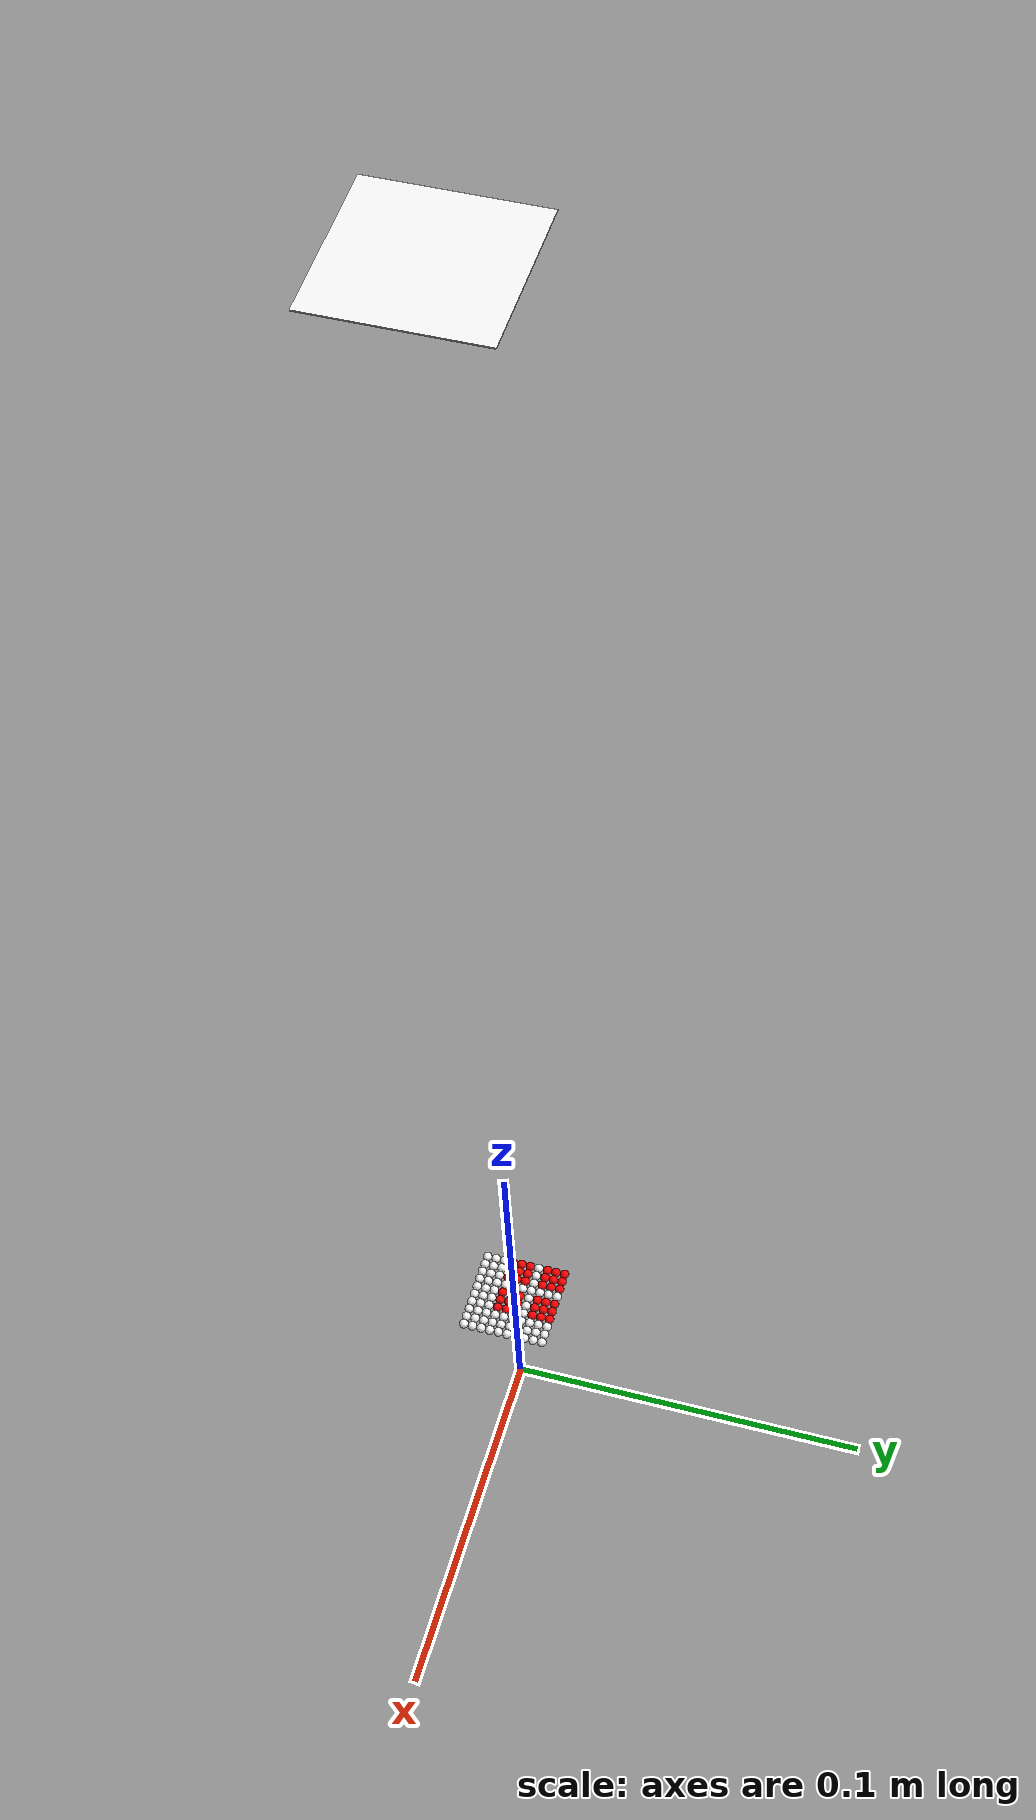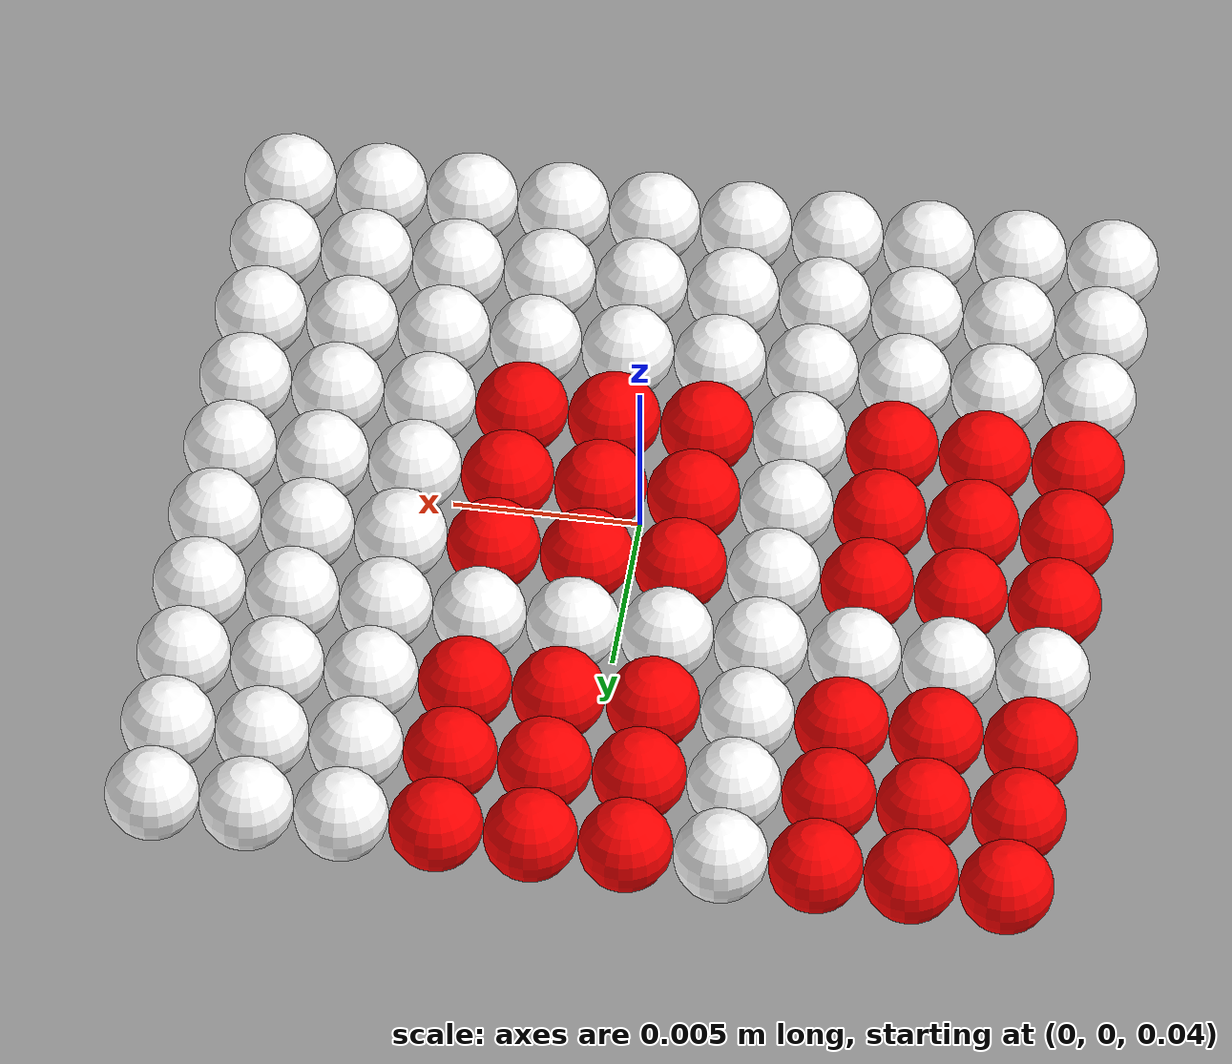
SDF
<sdf version='1.5'>
  <model name='spring_array10'>
    <pose>0 0 0 0 -0 0</pose>
    <link name='plane'>
      <pose>0 0 0.4 0 -0 0</pose>
      <inertial>
        <mass>20</mass>
      </inertial>
      <collision name='collision'>
        <geometry>
          <box>
            <size>0.0375 0.0375 0.00025</size>
          </box>
        </geometry>
        <surface>
          <friction>
            <ode>
              <mu>0</mu>
              <mu2>0</mu2>
            </ode>
          </friction>
        </surface>
      </collision>
      <visual name='visual'>
        <geometry>
          <box>
            <size>0.0375 0.0375 0.00025</size>
          </box>
        </geometry>
        <material>
          <ambient>1 1 1 1</ambient>
          <diffuse>1 1 1 1</diffuse>
          <specular>0.1 0.1 0.1 1</specular>
          <emissive>0 0 0 0</emissive>
        </material>
      </visual>
    </link>
    <joint name='plane_joint' type='prismatic'>
      <parent>world</parent>
      <child>plane</child>
      <axis>
        <xyz>0 0 1</xyz>
        <limit>
          <lower>1e+16</lower>
          <upper>-1e+16</upper>
        </limit>
        <use_parent_model_frame>1</use_parent_model_frame>
      </axis>
    </joint>
    <link name='spring_1'>
      <pose>-0.01125 0.01125 0.04 0 -0 0</pose>
      <inertial>
        <mass>0.00235</mass>
      </inertial>
      <collision name='sphere_collision'>
        <geometry>
          <sphere>
            <radius>0.00125</radius>
          </sphere>
        </geometry>
        <surface>
          <friction>
            <ode>
              <mu>0</mu>
              <mu2>0</mu2>
            </ode>
          </friction>
        </surface>
      </collision>
      <visual name='visual'>
        <geometry>
          <sphere>
            <radius>0.00125</radius>
          </sphere>
        </geometry>
        <material>
          <ambient>1 0 0 1</ambient>
          <diffuse>1 0 0 1</diffuse>
          <specular>0.1 0.1 0.1 1</specular>
          <emissive>0 0 0 0</emissive>
        </material>
      </visual>
    </link>
    <joint name='spring_joint_1' type='prismatic'>
      <parent>plane</parent>
      <child>spring_1</child>
      <axis>
        <xyz>0 0 1</xyz>
        <limit>
          <lower>-1e+16</lower>
          <upper>1e+16</upper>
        </limit>
        <use_parent_model_frame>1</use_parent_model_frame>
      </axis>
    </joint>
    <link name='spring_2'>
      <pose>-0.00875 0.01125 0.04 0 -0 0</pose>
      <inertial>
        <mass>0.00235</mass>
      </inertial>
      <collision name='sphere_collision'>
        <geometry>
          <sphere>
            <radius>0.00125</radius>
          </sphere>
        </geometry>
        <surface>
          <friction>
            <ode>
              <mu>0</mu>
              <mu2>0</mu2>
            </ode>
          </friction>
        </surface>
      </collision>
      <visual name='visual'>
        <geometry>
          <sphere>
            <radius>0.00125</radius>
          </sphere>
        </geometry>
        <material>
          <ambient>1 0 0 1</ambient>
          <diffuse>1 0 0 1</diffuse>
          <specular>0.1 0.1 0.1 1</specular>
          <emissive>0 0 0 0</emissive>
        </material>
      </visual>
    </link>
    <joint name='spring_joint_2' type='prismatic'>
      <parent>plane</parent>
      <child>spring_2</child>
      <axis>
        <xyz>0 0 1</xyz>
        <limit>
          <lower>-1e+16</lower>
          <upper>1e+16</upper>
        </limit>
        <use_parent_model_frame>1</use_parent_model_frame>
      </axis>
    </joint>
    <link name='spring_3'>
      <pose>-0.00625 0.01125 0.04 0 -0 0</pose>
      <inertial>
        <mass>0.00235</mass>
      </inertial>
      <collision name='sphere_collision'>
        <geometry>
          <sphere>
            <radius>0.00125</radius>
          </sphere>
        </geometry>
        <surface>
          <friction>
            <ode>
              <mu>0</mu>
              <mu2>0</mu2>
            </ode>
          </friction>
        </surface>
      </collision>
      <visual name='visual'>
        <geometry>
          <sphere>
            <radius>0.00125</radius>
          </sphere>
        </geometry>
        <material>
          <ambient>1 0 0 1</ambient>
          <diffuse>1 0 0 1</diffuse>
          <specular>0.1 0.1 0.1 1</specular>
          <emissive>0 0 0 0</emissive>
        </material>
      </visual>
    </link>
    <joint name='spring_joint_3' type='prismatic'>
      <parent>plane</parent>
      <child>spring_3</child>
      <axis>
        <xyz>0 0 1</xyz>
        <limit>
          <lower>-1e+16</lower>
          <upper>1e+16</upper>
        </limit>
        <use_parent_model_frame>1</use_parent_model_frame>
      </axis>
    </joint>
    <link name='spring_4'>
      <pose>-0.00375 0.01125 0.04 0 -0 0</pose>
      <inertial>
        <mass>0.00235</mass>
      </inertial>
      <collision name='sphere_collision'>
        <geometry>
          <sphere>
            <radius>0.00125</radius>
          </sphere>
        </geometry>
        <surface>
          <friction>
            <ode>
              <mu>0</mu>
              <mu2>0</mu2>
            </ode>
          </friction>
        </surface>
      </collision>
      <visual name='visual'>
        <geometry>
          <sphere>
            <radius>0.00125</radius>
          </sphere>
        </geometry>
        <material>
          <ambient>1 1 1 1</ambient>
          <diffuse>1 1 1 1</diffuse>
          <specular>0.1 0.1 0.1 1</specular>
          <emissive>0 0 0 0</emissive>
        </material>
      </visual>
    </link>
    <joint name='spring_joint_4' type='prismatic'>
      <parent>plane</parent>
      <child>spring_4</child>
      <axis>
        <xyz>0 0 1</xyz>
        <limit>
          <lower>-1e+16</lower>
          <upper>1e+16</upper>
        </limit>
        <use_parent_model_frame>1</use_parent_model_frame>
      </axis>
    </joint>
    <link name='spring_5'>
      <pose>-0.00125 0.01125 0.04 0 -0 0</pose>
      <inertial>
        <mass>0.00235</mass>
      </inertial>
      <collision name='sphere_collision'>
        <geometry>
          <sphere>
            <radius>0.00125</radius>
          </sphere>
        </geometry>
        <surface>
          <friction>
            <ode>
              <mu>0</mu>
              <mu2>0</mu2>
            </ode>
          </friction>
        </surface>
      </collision>
      <visual name='visual'>
        <geometry>
          <sphere>
            <radius>0.00125</radius>
          </sphere>
        </geometry>
        <material>
          <ambient>1 0 0 1</ambient>
          <diffuse>1 0 0 1</diffuse>
          <specular>0.1 0.1 0.1 1</specular>
          <emissive>0 0 0 0</emissive>
        </material>
      </visual>
    </link>
    <joint name='spring_joint_5' type='prismatic'>
      <parent>plane</parent>
      <child>spring_5</child>
      <axis>
        <xyz>0 0 1</xyz>
        <limit>
          <lower>-1e+16</lower>
          <upper>1e+16</upper>
        </limit>
        <use_parent_model_frame>1</use_parent_model_frame>
      </axis>
    </joint>
    <link name='spring_6'>
      <pose>0.00125 0.01125 0.04 0 -0 0</pose>
      <inertial>
        <mass>0.00235</mass>
      </inertial>
      <collision name='sphere_collision'>
        <geometry>
          <sphere>
            <radius>0.00125</radius>
          </sphere>
        </geometry>
        <surface>
          <friction>
            <ode>
              <mu>0</mu>
              <mu2>0</mu2>
            </ode>
          </friction>
        </surface>
      </collision>
      <visual name='visual'>
        <geometry>
          <sphere>
            <radius>0.00125</radius>
          </sphere>
        </geometry>
        <material>
          <ambient>1 0 0 1</ambient>
          <diffuse>1 0 0 1</diffuse>
          <specular>0.1 0.1 0.1 1</specular>
          <emissive>0 0 0 0</emissive>
        </material>
      </visual>
    </link>
    <joint name='spring_joint_6' type='prismatic'>
      <parent>plane</parent>
      <child>spring_6</child>
      <axis>
        <xyz>0 0 1</xyz>
        <limit>
          <lower>-1e+16</lower>
          <upper>1e+16</upper>
        </limit>
        <use_parent_model_frame>1</use_parent_model_frame>
      </axis>
    </joint>
    <link name='spring_7'>
      <pose>0.00375 0.01125 0.04 0 -0 0</pose>
      <inertial>
        <mass>0.00235</mass>
      </inertial>
      <collision name='sphere_collision'>
        <geometry>
          <sphere>
            <radius>0.00125</radius>
          </sphere>
        </geometry>
        <surface>
          <friction>
            <ode>
              <mu>0</mu>
              <mu2>0</mu2>
            </ode>
          </friction>
        </surface>
      </collision>
      <visual name='visual'>
        <geometry>
          <sphere>
            <radius>0.00125</radius>
          </sphere>
        </geometry>
        <material>
          <ambient>1 0 0 1</ambient>
          <diffuse>1 0 0 1</diffuse>
          <specular>0.1 0.1 0.1 1</specular>
          <emissive>0 0 0 0</emissive>
        </material>
      </visual>
    </link>
    <joint name='spring_joint_7' type='prismatic'>
      <parent>plane</parent>
      <child>spring_7</child>
      <axis>
        <xyz>0 0 1</xyz>
        <limit>
          <lower>-1e+16</lower>
          <upper>1e+16</upper>
        </limit>
        <use_parent_model_frame>1</use_parent_model_frame>
      </axis>
    </joint>
    <link name='spring_8'>
      <pose>0.00625 0.01125 0.04 0 -0 0</pose>
      <inertial>
        <mass>0.00235</mass>
      </inertial>
      <collision name='sphere_collision'>
        <geometry>
          <sphere>
            <radius>0.00125</radius>
          </sphere>
        </geometry>
        <surface>
          <friction>
            <ode>
              <mu>0</mu>
              <mu2>0</mu2>
            </ode>
          </friction>
        </surface>
      </collision>
      <visual name='visual'>
        <geometry>
          <sphere>
            <radius>0.00125</radius>
          </sphere>
        </geometry>
        <material>
          <ambient>1 1 1 1</ambient>
          <diffuse>1 1 1 1</diffuse>
          <specular>0.1 0.1 0.1 1</specular>
          <emissive>0 0 0 0</emissive>
        </material>
      </visual>
    </link>
    <joint name='spring_joint_8' type='prismatic'>
      <parent>plane</parent>
      <child>spring_8</child>
      <axis>
        <xyz>0 0 1</xyz>
        <limit>
          <lower>-1e+16</lower>
          <upper>1e+16</upper>
        </limit>
        <use_parent_model_frame>1</use_parent_model_frame>
      </axis>
    </joint>
    <link name='spring_9'>
      <pose>0.00875 0.01125 0.04 0 -0 0</pose>
      <inertial>
        <mass>0.00235</mass>
      </inertial>
      <collision name='sphere_collision'>
        <geometry>
          <sphere>
            <radius>0.00125</radius>
          </sphere>
        </geometry>
        <surface>
          <friction>
            <ode>
              <mu>0</mu>
              <mu2>0</mu2>
            </ode>
          </friction>
        </surface>
      </collision>
      <visual name='visual'>
        <geometry>
          <sphere>
            <radius>0.00125</radius>
          </sphere>
        </geometry>
        <material>
          <ambient>1 1 1 1</ambient>
          <diffuse>1 1 1 1</diffuse>
          <specular>0.1 0.1 0.1 1</specular>
          <emissive>0 0 0 0</emissive>
        </material>
      </visual>
    </link>
    <joint name='spring_joint_9' type='prismatic'>
      <parent>plane</parent>
      <child>spring_9</child>
      <axis>
        <xyz>0 0 1</xyz>
        <limit>
          <lower>-1e+16</lower>
          <upper>1e+16</upper>
        </limit>
        <use_parent_model_frame>1</use_parent_model_frame>
      </axis>
    </joint>
    <link name='spring_10'>
      <pose>0.01125 0.01125 0.04 0 -0 0</pose>
      <inertial>
        <mass>0.00235</mass>
      </inertial>
      <collision name='sphere_collision'>
        <geometry>
          <sphere>
            <radius>0.00125</radius>
          </sphere>
        </geometry>
        <surface>
          <friction>
            <ode>
              <mu>0</mu>
              <mu2>0</mu2>
            </ode>
          </friction>
        </surface>
      </collision>
      <visual name='visual'>
        <geometry>
          <sphere>
            <radius>0.00125</radius>
          </sphere>
        </geometry>
        <material>
          <ambient>1 1 1 1</ambient>
          <diffuse>1 1 1 1</diffuse>
          <specular>0.1 0.1 0.1 1</specular>
          <emissive>0 0 0 0</emissive>
        </material>
      </visual>
    </link>
    <joint name='spring_joint_10' type='prismatic'>
      <parent>plane</parent>
      <child>spring_10</child>
      <axis>
        <xyz>0 0 1</xyz>
        <limit>
          <lower>-1e+16</lower>
          <upper>1e+16</upper>
        </limit>
        <use_parent_model_frame>1</use_parent_model_frame>
      </axis>
    </joint>
    <link name='spring_11'>
      <pose>-0.01125 0.00875 0.04 0 -0 0</pose>
      <inertial>
        <mass>0.00235</mass>
      </inertial>
      <collision name='sphere_collision'>
        <geometry>
          <sphere>
            <radius>0.00125</radius>
          </sphere>
        </geometry>
        <surface>
          <friction>
            <ode>
              <mu>0</mu>
              <mu2>0</mu2>
            </ode>
          </friction>
        </surface>
      </collision>
      <visual name='visual'>
        <geometry>
          <sphere>
            <radius>0.00125</radius>
          </sphere>
        </geometry>
        <material>
          <ambient>1 0 0 1</ambient>
          <diffuse>1 0 0 1</diffuse>
          <specular>0.1 0.1 0.1 1</specular>
          <emissive>0 0 0 0</emissive>
        </material>
      </visual>
    </link>
    <joint name='spring_joint_11' type='prismatic'>
      <parent>plane</parent>
      <child>spring_11</child>
      <axis>
        <xyz>0 0 1</xyz>
        <limit>
          <lower>-1e+16</lower>
          <upper>1e+16</upper>
        </limit>
        <use_parent_model_frame>1</use_parent_model_frame>
      </axis>
    </joint>
    <link name='spring_12'>
      <pose>-0.00875 0.00875 0.04 0 -0 0</pose>
      <inertial>
        <mass>0.00235</mass>
      </inertial>
      <collision name='sphere_collision'>
        <geometry>
          <sphere>
            <radius>0.00125</radius>
          </sphere>
        </geometry>
        <surface>
          <friction>
            <ode>
              <mu>0</mu>
              <mu2>0</mu2>
            </ode>
          </friction>
        </surface>
      </collision>
      <visual name='visual'>
        <geometry>
          <sphere>
            <radius>0.00125</radius>
          </sphere>
        </geometry>
        <material>
          <ambient>1 0 0 1</ambient>
          <diffuse>1 0 0 1</diffuse>
          <specular>0.1 0.1 0.1 1</specular>
          <emissive>0 0 0 0</emissive>
        </material>
      </visual>
    </link>
    <joint name='spring_joint_12' type='prismatic'>
      <parent>plane</parent>
      <child>spring_12</child>
      <axis>
        <xyz>0 0 1</xyz>
        <limit>
          <lower>-1e+16</lower>
          <upper>1e+16</upper>
        </limit>
        <use_parent_model_frame>1</use_parent_model_frame>
      </axis>
    </joint>
    <link name='spring_13'>
      <pose>-0.00625 0.00875 0.04 0 -0 0</pose>
      <inertial>
        <mass>0.00235</mass>
      </inertial>
      <collision name='sphere_collision'>
        <geometry>
          <sphere>
            <radius>0.00125</radius>
          </sphere>
        </geometry>
        <surface>
          <friction>
            <ode>
              <mu>0</mu>
              <mu2>0</mu2>
            </ode>
          </friction>
        </surface>
      </collision>
      <visual name='visual'>
        <geometry>
          <sphere>
            <radius>0.00125</radius>
          </sphere>
        </geometry>
        <material>
          <ambient>1 0 0 1</ambient>
          <diffuse>1 0 0 1</diffuse>
          <specular>0.1 0.1 0.1 1</specular>
          <emissive>0 0 0 0</emissive>
        </material>
      </visual>
    </link>
    <joint name='spring_joint_13' type='prismatic'>
      <parent>plane</parent>
      <child>spring_13</child>
      <axis>
        <xyz>0 0 1</xyz>
        <limit>
          <lower>-1e+16</lower>
          <upper>1e+16</upper>
        </limit>
        <use_parent_model_frame>1</use_parent_model_frame>
      </axis>
    </joint>
    <link name='spring_14'>
      <pose>-0.00375 0.00875 0.04 0 -0 0</pose>
      <inertial>
        <mass>0.00235</mass>
      </inertial>
      <collision name='sphere_collision'>
        <geometry>
          <sphere>
            <radius>0.00125</radius>
          </sphere>
        </geometry>
        <surface>
          <friction>
            <ode>
              <mu>0</mu>
              <mu2>0</mu2>
            </ode>
          </friction>
        </surface>
      </collision>
      <visual name='visual'>
        <geometry>
          <sphere>
            <radius>0.00125</radius>
          </sphere>
        </geometry>
        <material>
          <ambient>1 1 1 1</ambient>
          <diffuse>1 1 1 1</diffuse>
          <specular>0.1 0.1 0.1 1</specular>
          <emissive>0 0 0 0</emissive>
        </material>
      </visual>
    </link>
    <joint name='spring_joint_14' type='prismatic'>
      <parent>plane</parent>
      <child>spring_14</child>
      <axis>
        <xyz>0 0 1</xyz>
        <limit>
          <lower>-1e+16</lower>
          <upper>1e+16</upper>
        </limit>
        <use_parent_model_frame>1</use_parent_model_frame>
      </axis>
    </joint>
    <link name='spring_15'>
      <pose>-0.00125 0.00875 0.04 0 -0 0</pose>
      <inertial>
        <mass>0.00235</mass>
      </inertial>
      <collision name='sphere_collision'>
        <geometry>
          <sphere>
            <radius>0.00125</radius>
          </sphere>
        </geometry>
        <surface>
          <friction>
            <ode>
              <mu>0</mu>
              <mu2>0</mu2>
            </ode>
          </friction>
        </surface>
      </collision>
      <visual name='visual'>
        <geometry>
          <sphere>
            <radius>0.00125</radius>
          </sphere>
        </geometry>
        <material>
          <ambient>1 0 0 1</ambient>
          <diffuse>1 0 0 1</diffuse>
          <specular>0.1 0.1 0.1 1</specular>
          <emissive>0 0 0 0</emissive>
        </material>
      </visual>
    </link>
    <joint name='spring_joint_15' type='prismatic'>
      <parent>plane</parent>
      <child>spring_15</child>
      <axis>
        <xyz>0 0 1</xyz>
        <limit>
          <lower>-1e+16</lower>
          <upper>1e+16</upper>
        </limit>
        <use_parent_model_frame>1</use_parent_model_frame>
      </axis>
    </joint>
    <link name='spring_16'>
      <pose>0.00125 0.00875 0.04 0 -0 0</pose>
      <inertial>
        <mass>0.00235</mass>
      </inertial>
      <collision name='sphere_collision'>
        <geometry>
          <sphere>
            <radius>0.00125</radius>
          </sphere>
        </geometry>
        <surface>
          <friction>
            <ode>
              <mu>0</mu>
              <mu2>0</mu2>
            </ode>
          </friction>
        </surface>
      </collision>
      <visual name='visual'>
        <geometry>
          <sphere>
            <radius>0.00125</radius>
          </sphere>
        </geometry>
        <material>
          <ambient>1 0 0 1</ambient>
          <diffuse>1 0 0 1</diffuse>
          <specular>0.1 0.1 0.1 1</specular>
          <emissive>0 0 0 0</emissive>
        </material>
      </visual>
    </link>
    <joint name='spring_joint_16' type='prismatic'>
      <parent>plane</parent>
      <child>spring_16</child>
      <axis>
        <xyz>0 0 1</xyz>
        <limit>
          <lower>-1e+16</lower>
          <upper>1e+16</upper>
        </limit>
        <use_parent_model_frame>1</use_parent_model_frame>
      </axis>
    </joint>
    <link name='spring_17'>
      <pose>0.00375 0.00875 0.04 0 -0 0</pose>
      <inertial>
        <mass>0.00235</mass>
      </inertial>
      <collision name='sphere_collision'>
        <geometry>
          <sphere>
            <radius>0.00125</radius>
          </sphere>
        </geometry>
        <surface>
          <friction>
            <ode>
              <mu>0</mu>
              <mu2>0</mu2>
            </ode>
          </friction>
        </surface>
      </collision>
      <visual name='visual'>
        <geometry>
          <sphere>
            <radius>0.00125</radius>
          </sphere>
        </geometry>
        <material>
          <ambient>1 0 0 1</ambient>
          <diffuse>1 0 0 1</diffuse>
          <specular>0.1 0.1 0.1 1</specular>
          <emissive>0 0 0 0</emissive>
        </material>
      </visual>
    </link>
    <joint name='spring_joint_17' type='prismatic'>
      <parent>plane</parent>
      <child>spring_17</child>
      <axis>
        <xyz>0 0 1</xyz>
        <limit>
          <lower>-1e+16</lower>
          <upper>1e+16</upper>
        </limit>
        <use_parent_model_frame>1</use_parent_model_frame>
      </axis>
    </joint>
    <link name='spring_18'>
      <pose>0.00625 0.00875 0.04 0 -0 0</pose>
      <inertial>
        <mass>0.00235</mass>
      </inertial>
      <collision name='sphere_collision'>
        <geometry>
          <sphere>
            <radius>0.00125</radius>
          </sphere>
        </geometry>
        <surface>
          <friction>
            <ode>
              <mu>0</mu>
              <mu2>0</mu2>
            </ode>
          </friction>
        </surface>
      </collision>
      <visual name='visual'>
        <geometry>
          <sphere>
            <radius>0.00125</radius>
          </sphere>
        </geometry>
        <material>
          <ambient>1 1 1 1</ambient>
          <diffuse>1 1 1 1</diffuse>
          <specular>0.1 0.1 0.1 1</specular>
          <emissive>0 0 0 0</emissive>
        </material>
      </visual>
    </link>
    <joint name='spring_joint_18' type='prismatic'>
      <parent>plane</parent>
      <child>spring_18</child>
      <axis>
        <xyz>0 0 1</xyz>
        <limit>
          <lower>-1e+16</lower>
          <upper>1e+16</upper>
        </limit>
        <use_parent_model_frame>1</use_parent_model_frame>
      </axis>
    </joint>
    <link name='spring_19'>
      <pose>0.00875 0.00875 0.04 0 -0 0</pose>
      <inertial>
        <mass>0.00235</mass>
      </inertial>
      <collision name='sphere_collision'>
        <geometry>
          <sphere>
            <radius>0.00125</radius>
          </sphere>
        </geometry>
        <surface>
          <friction>
            <ode>
              <mu>0</mu>
              <mu2>0</mu2>
            </ode>
          </friction>
        </surface>
      </collision>
      <visual name='visual'>
        <geometry>
          <sphere>
            <radius>0.00125</radius>
          </sphere>
        </geometry>
        <material>
          <ambient>1 1 1 1</ambient>
          <diffuse>1 1 1 1</diffuse>
          <specular>0.1 0.1 0.1 1</specular>
          <emissive>0 0 0 0</emissive>
        </material>
      </visual>
    </link>
    <joint name='spring_joint_19' type='prismatic'>
      <parent>plane</parent>
      <child>spring_19</child>
      <axis>
        <xyz>0 0 1</xyz>
        <limit>
          <lower>-1e+16</lower>
          <upper>1e+16</upper>
        </limit>
        <use_parent_model_frame>1</use_parent_model_frame>
      </axis>
    </joint>
    <link name='spring_20'>
      <pose>0.01125 0.00875 0.04 0 -0 0</pose>
      <inertial>
        <mass>0.00235</mass>
      </inertial>
      <collision name='sphere_collision'>
        <geometry>
          <sphere>
            <radius>0.00125</radius>
          </sphere>
        </geometry>
        <surface>
          <friction>
            <ode>
              <mu>0</mu>
              <mu2>0</mu2>
            </ode>
          </friction>
        </surface>
      </collision>
      <visual name='visual'>
        <geometry>
          <sphere>
            <radius>0.00125</radius>
          </sphere>
        </geometry>
        <material>
          <ambient>1 1 1 1</ambient>
          <diffuse>1 1 1 1</diffuse>
          <specular>0.1 0.1 0.1 1</specular>
          <emissive>0 0 0 0</emissive>
        </material>
      </visual>
    </link>
    <joint name='spring_joint_20' type='prismatic'>
      <parent>plane</parent>
      <child>spring_20</child>
      <axis>
        <xyz>0 0 1</xyz>
        <limit>
          <lower>-1e+16</lower>
          <upper>1e+16</upper>
        </limit>
        <use_parent_model_frame>1</use_parent_model_frame>
      </axis>
    </joint>
    <link name='spring_21'>
      <pose>-0.01125 0.00625 0.04 0 -0 0</pose>
      <inertial>
        <mass>0.00235</mass>
      </inertial>
      <collision name='sphere_collision'>
        <geometry>
          <sphere>
            <radius>0.00125</radius>
          </sphere>
        </geometry>
        <surface>
          <friction>
            <ode>
              <mu>0</mu>
              <mu2>0</mu2>
            </ode>
          </friction>
        </surface>
      </collision>
      <visual name='visual'>
        <geometry>
          <sphere>
            <radius>0.00125</radius>
          </sphere>
        </geometry>
        <material>
          <ambient>1 0 0 1</ambient>
          <diffuse>1 0 0 1</diffuse>
          <specular>0.1 0.1 0.1 1</specular>
          <emissive>0 0 0 0</emissive>
        </material>
      </visual>
    </link>
    <joint name='spring_joint_21' type='prismatic'>
      <parent>plane</parent>
      <child>spring_21</child>
      <axis>
        <xyz>0 0 1</xyz>
        <limit>
          <lower>-1e+16</lower>
          <upper>1e+16</upper>
        </limit>
        <use_parent_model_frame>1</use_parent_model_frame>
      </axis>
    </joint>
    <link name='spring_22'>
      <pose>-0.00875 0.00625 0.04 0 -0 0</pose>
      <inertial>
        <mass>0.00235</mass>
      </inertial>
      <collision name='sphere_collision'>
        <geometry>
          <sphere>
            <radius>0.00125</radius>
          </sphere>
        </geometry>
        <surface>
          <friction>
            <ode>
              <mu>0</mu>
              <mu2>0</mu2>
            </ode>
          </friction>
        </surface>
      </collision>
      <visual name='visual'>
        <geometry>
          <sphere>
            <radius>0.00125</radius>
          </sphere>
        </geometry>
        <material>
          <ambient>1 0 0 1</ambient>
          <diffuse>1 0 0 1</diffuse>
          <specular>0.1 0.1 0.1 1</specular>
          <emissive>0 0 0 0</emissive>
        </material>
      </visual>
    </link>
    <joint name='spring_joint_22' type='prismatic'>
      <parent>plane</parent>
      <child>spring_22</child>
      <axis>
        <xyz>0 0 1</xyz>
        <limit>
          <lower>-1e+16</lower>
          <upper>1e+16</upper>
        </limit>
        <use_parent_model_frame>1</use_parent_model_frame>
      </axis>
    </joint>
    <link name='spring_23'>
      <pose>-0.00625 0.00625 0.04 0 -0 0</pose>
      <inertial>
        <mass>0.00235</mass>
      </inertial>
      <collision name='sphere_collision'>
        <geometry>
          <sphere>
            <radius>0.00125</radius>
          </sphere>
        </geometry>
        <surface>
          <friction>
            <ode>
              <mu>0</mu>
              <mu2>0</mu2>
            </ode>
          </friction>
        </surface>
      </collision>
      <visual name='visual'>
        <geometry>
          <sphere>
            <radius>0.00125</radius>
          </sphere>
        </geometry>
        <material>
          <ambient>1 0 0 1</ambient>
          <diffuse>1 0 0 1</diffuse>
          <specular>0.1 0.1 0.1 1</specular>
          <emissive>0 0 0 0</emissive>
        </material>
      </visual>
    </link>
    <joint name='spring_joint_23' type='prismatic'>
      <parent>plane</parent>
      <child>spring_23</child>
      <axis>
        <xyz>0 0 1</xyz>
        <limit>
          <lower>-1e+16</lower>
          <upper>1e+16</upper>
        </limit>
        <use_parent_model_frame>1</use_parent_model_frame>
      </axis>
    </joint>
    <link name='spring_24'>
      <pose>-0.00375 0.00625 0.04 0 -0 0</pose>
      <inertial>
        <mass>0.00235</mass>
      </inertial>
      <collision name='sphere_collision'>
        <geometry>
          <sphere>
            <radius>0.00125</radius>
          </sphere>
        </geometry>
        <surface>
          <friction>
            <ode>
              <mu>0</mu>
              <mu2>0</mu2>
            </ode>
          </friction>
        </surface>
      </collision>
      <visual name='visual'>
        <geometry>
          <sphere>
            <radius>0.00125</radius>
          </sphere>
        </geometry>
        <material>
          <ambient>1 1 1 1</ambient>
          <diffuse>1 1 1 1</diffuse>
          <specular>0.1 0.1 0.1 1</specular>
          <emissive>0 0 0 0</emissive>
        </material>
      </visual>
    </link>
    <joint name='spring_joint_24' type='prismatic'>
      <parent>plane</parent>
      <child>spring_24</child>
      <axis>
        <xyz>0 0 1</xyz>
        <limit>
          <lower>-1e+16</lower>
          <upper>1e+16</upper>
        </limit>
        <use_parent_model_frame>1</use_parent_model_frame>
      </axis>
    </joint>
    <link name='spring_25'>
      <pose>-0.00125 0.00625 0.04 0 -0 0</pose>
      <inertial>
        <mass>0.00235</mass>
      </inertial>
      <collision name='sphere_collision'>
        <geometry>
          <sphere>
            <radius>0.00125</radius>
          </sphere>
        </geometry>
        <surface>
          <friction>
            <ode>
              <mu>0</mu>
              <mu2>0</mu2>
            </ode>
          </friction>
        </surface>
      </collision>
      <visual name='visual'>
        <geometry>
          <sphere>
            <radius>0.00125</radius>
          </sphere>
        </geometry>
        <material>
          <ambient>1 0 0 1</ambient>
          <diffuse>1 0 0 1</diffuse>
          <specular>0.1 0.1 0.1 1</specular>
          <emissive>0 0 0 0</emissive>
        </material>
      </visual>
    </link>
    <joint name='spring_joint_25' type='prismatic'>
      <parent>plane</parent>
      <child>spring_25</child>
      <axis>
        <xyz>0 0 1</xyz>
        <limit>
          <lower>-1e+16</lower>
          <upper>1e+16</upper>
        </limit>
        <use_parent_model_frame>1</use_parent_model_frame>
      </axis>
    </joint>
    <link name='spring_26'>
      <pose>0.00125 0.00625 0.04 0 -0 0</pose>
      <inertial>
        <mass>0.00235</mass>
      </inertial>
      <collision name='sphere_collision'>
        <geometry>
          <sphere>
            <radius>0.00125</radius>
          </sphere>
        </geometry>
        <surface>
          <friction>
            <ode>
              <mu>0</mu>
              <mu2>0</mu2>
            </ode>
          </friction>
        </surface>
      </collision>
      <visual name='visual'>
        <geometry>
          <sphere>
            <radius>0.00125</radius>
          </sphere>
        </geometry>
        <material>
          <ambient>1 0 0 1</ambient>
          <diffuse>1 0 0 1</diffuse>
          <specular>0.1 0.1 0.1 1</specular>
          <emissive>0 0 0 0</emissive>
        </material>
      </visual>
    </link>
    <joint name='spring_joint_26' type='prismatic'>
      <parent>plane</parent>
      <child>spring_26</child>
      <axis>
        <xyz>0 0 1</xyz>
        <limit>
          <lower>-1e+16</lower>
          <upper>1e+16</upper>
        </limit>
        <use_parent_model_frame>1</use_parent_model_frame>
      </axis>
    </joint>
    <link name='spring_27'>
      <pose>0.00375 0.00625 0.04 0 -0 0</pose>
      <inertial>
        <mass>0.00235</mass>
      </inertial>
      <collision name='sphere_collision'>
        <geometry>
          <sphere>
            <radius>0.00125</radius>
          </sphere>
        </geometry>
        <surface>
          <friction>
            <ode>
              <mu>0</mu>
              <mu2>0</mu2>
            </ode>
          </friction>
        </surface>
      </collision>
      <visual name='visual'>
        <geometry>
          <sphere>
            <radius>0.00125</radius>
          </sphere>
        </geometry>
        <material>
          <ambient>1 0 0 1</ambient>
          <diffuse>1 0 0 1</diffuse>
          <specular>0.1 0.1 0.1 1</specular>
          <emissive>0 0 0 0</emissive>
        </material>
      </visual>
    </link>
    <joint name='spring_joint_27' type='prismatic'>
      <parent>plane</parent>
      <child>spring_27</child>
      <axis>
        <xyz>0 0 1</xyz>
        <limit>
          <lower>-1e+16</lower>
          <upper>1e+16</upper>
        </limit>
        <use_parent_model_frame>1</use_parent_model_frame>
      </axis>
    </joint>
    <link name='spring_28'>
      <pose>0.00625 0.00625 0.04 0 -0 0</pose>
      <inertial>
        <mass>0.00235</mass>
      </inertial>
      <collision name='sphere_collision'>
        <geometry>
          <sphere>
            <radius>0.00125</radius>
          </sphere>
        </geometry>
        <surface>
          <friction>
            <ode>
              <mu>0</mu>
              <mu2>0</mu2>
            </ode>
          </friction>
        </surface>
      </collision>
      <visual name='visual'>
        <geometry>
          <sphere>
            <radius>0.00125</radius>
          </sphere>
        </geometry>
        <material>
          <ambient>1 1 1 1</ambient>
          <diffuse>1 1 1 1</diffuse>
          <specular>0.1 0.1 0.1 1</specular>
          <emissive>0 0 0 0</emissive>
        </material>
      </visual>
    </link>
    <joint name='spring_joint_28' type='prismatic'>
      <parent>plane</parent>
      <child>spring_28</child>
      <axis>
        <xyz>0 0 1</xyz>
        <limit>
          <lower>-1e+16</lower>
          <upper>1e+16</upper>
        </limit>
        <use_parent_model_frame>1</use_parent_model_frame>
      </axis>
    </joint>
    <link name='spring_29'>
      <pose>0.00875 0.00625 0.04 0 -0 0</pose>
      <inertial>
        <mass>0.00235</mass>
      </inertial>
      <collision name='sphere_collision'>
        <geometry>
          <sphere>
            <radius>0.00125</radius>
          </sphere>
        </geometry>
        <surface>
          <friction>
            <ode>
              <mu>0</mu>
              <mu2>0</mu2>
            </ode>
          </friction>
        </surface>
      </collision>
      <visual name='visual'>
        <geometry>
          <sphere>
            <radius>0.00125</radius>
          </sphere>
        </geometry>
        <material>
          <ambient>1 1 1 1</ambient>
          <diffuse>1 1 1 1</diffuse>
          <specular>0.1 0.1 0.1 1</specular>
          <emissive>0 0 0 0</emissive>
        </material>
      </visual>
    </link>
    <joint name='spring_joint_29' type='prismatic'>
      <parent>plane</parent>
      <child>spring_29</child>
      <axis>
        <xyz>0 0 1</xyz>
        <limit>
          <lower>-1e+16</lower>
          <upper>1e+16</upper>
        </limit>
        <use_parent_model_frame>1</use_parent_model_frame>
      </axis>
    </joint>
    <link name='spring_30'>
      <pose>0.01125 0.00625 0.04 0 -0 0</pose>
      <inertial>
        <mass>0.00235</mass>
      </inertial>
      <collision name='sphere_collision'>
        <geometry>
          <sphere>
            <radius>0.00125</radius>
          </sphere>
        </geometry>
        <surface>
          <friction>
            <ode>
              <mu>0</mu>
              <mu2>0</mu2>
            </ode>
          </friction>
        </surface>
      </collision>
      <visual name='visual'>
        <geometry>
          <sphere>
            <radius>0.00125</radius>
          </sphere>
        </geometry>
        <material>
          <ambient>1 1 1 1</ambient>
          <diffuse>1 1 1 1</diffuse>
          <specular>0.1 0.1 0.1 1</specular>
          <emissive>0 0 0 0</emissive>
        </material>
      </visual>
    </link>
    <joint name='spring_joint_30' type='prismatic'>
      <parent>plane</parent>
      <child>spring_30</child>
      <axis>
        <xyz>0 0 1</xyz>
        <limit>
          <lower>-1e+16</lower>
          <upper>1e+16</upper>
        </limit>
        <use_parent_model_frame>1</use_parent_model_frame>
      </axis>
    </joint>
    <link name='spring_31'>
      <pose>-0.01125 0.00375 0.04 0 -0 0</pose>
      <inertial>
        <mass>0.00235</mass>
      </inertial>
      <collision name='sphere_collision'>
        <geometry>
          <sphere>
            <radius>0.00125</radius>
          </sphere>
        </geometry>
        <surface>
          <friction>
            <ode>
              <mu>0</mu>
              <mu2>0</mu2>
            </ode>
          </friction>
        </surface>
      </collision>
      <visual name='visual'>
        <geometry>
          <sphere>
            <radius>0.00125</radius>
          </sphere>
        </geometry>
        <material>
          <ambient>1 1 1 1</ambient>
          <diffuse>1 1 1 1</diffuse>
          <specular>0.1 0.1 0.1 1</specular>
          <emissive>0 0 0 0</emissive>
        </material>
      </visual>
    </link>
    <joint name='spring_joint_31' type='prismatic'>
      <parent>plane</parent>
      <child>spring_31</child>
      <axis>
        <xyz>0 0 1</xyz>
        <limit>
          <lower>-1e+16</lower>
          <upper>1e+16</upper>
        </limit>
        <use_parent_model_frame>1</use_parent_model_frame>
      </axis>
    </joint>
    <link name='spring_32'>
      <pose>-0.00875 0.00375 0.04 0 -0 0</pose>
      <inertial>
        <mass>0.00235</mass>
      </inertial>
      <collision name='sphere_collision'>
        <geometry>
          <sphere>
            <radius>0.00125</radius>
          </sphere>
        </geometry>
        <surface>
          <friction>
            <ode>
              <mu>0</mu>
              <mu2>0</mu2>
            </ode>
          </friction>
        </surface>
      </collision>
      <visual name='visual'>
        <geometry>
          <sphere>
            <radius>0.00125</radius>
          </sphere>
        </geometry>
        <material>
          <ambient>1 1 1 1</ambient>
          <diffuse>1 1 1 1</diffuse>
          <specular>0.1 0.1 0.1 1</specular>
          <emissive>0 0 0 0</emissive>
        </material>
      </visual>
    </link>
    <joint name='spring_joint_32' type='prismatic'>
      <parent>plane</parent>
      <child>spring_32</child>
      <axis>
        <xyz>0 0 1</xyz>
        <limit>
          <lower>-1e+16</lower>
          <upper>1e+16</upper>
        </limit>
        <use_parent_model_frame>1</use_parent_model_frame>
      </axis>
    </joint>
    <link name='spring_33'>
      <pose>-0.00625 0.00375 0.04 0 -0 0</pose>
      <inertial>
        <mass>0.00235</mass>
      </inertial>
      <collision name='sphere_collision'>
        <geometry>
          <sphere>
            <radius>0.00125</radius>
          </sphere>
        </geometry>
        <surface>
          <friction>
            <ode>
              <mu>0</mu>
              <mu2>0</mu2>
            </ode>
          </friction>
        </surface>
      </collision>
      <visual name='visual'>
        <geometry>
          <sphere>
            <radius>0.00125</radius>
          </sphere>
        </geometry>
        <material>
          <ambient>1 1 1 1</ambient>
          <diffuse>1 1 1 1</diffuse>
          <specular>0.1 0.1 0.1 1</specular>
          <emissive>0 0 0 0</emissive>
        </material>
      </visual>
    </link>
    <joint name='spring_joint_33' type='prismatic'>
      <parent>plane</parent>
      <child>spring_33</child>
      <axis>
        <xyz>0 0 1</xyz>
        <limit>
          <lower>-1e+16</lower>
          <upper>1e+16</upper>
        </limit>
        <use_parent_model_frame>1</use_parent_model_frame>
      </axis>
    </joint>
    <link name='spring_34'>
      <pose>-0.00375 0.00375 0.04 0 -0 0</pose>
      <inertial>
        <mass>0.00235</mass>
      </inertial>
      <collision name='sphere_collision'>
        <geometry>
          <sphere>
            <radius>0.00125</radius>
          </sphere>
        </geometry>
        <surface>
          <friction>
            <ode>
              <mu>0</mu>
              <mu2>0</mu2>
            </ode>
          </friction>
        </surface>
      </collision>
      <visual name='visual'>
        <geometry>
          <sphere>
            <radius>0.00125</radius>
          </sphere>
        </geometry>
        <material>
          <ambient>1 1 1 1</ambient>
          <diffuse>1 1 1 1</diffuse>
          <specular>0.1 0.1 0.1 1</specular>
          <emissive>0 0 0 0</emissive>
        </material>
      </visual>
    </link>
    <joint name='spring_joint_34' type='prismatic'>
      <parent>plane</parent>
      <child>spring_34</child>
      <axis>
        <xyz>0 0 1</xyz>
        <limit>
          <lower>-1e+16</lower>
          <upper>1e+16</upper>
        </limit>
        <use_parent_model_frame>1</use_parent_model_frame>
      </axis>
    </joint>
    <link name='spring_35'>
      <pose>-0.00125 0.00375 0.04 0 -0 0</pose>
      <inertial>
        <mass>0.00235</mass>
      </inertial>
      <collision name='sphere_collision'>
        <geometry>
          <sphere>
            <radius>0.00125</radius>
          </sphere>
        </geometry>
        <surface>
          <friction>
            <ode>
              <mu>0</mu>
              <mu2>0</mu2>
            </ode>
          </friction>
        </surface>
      </collision>
      <visual name='visual'>
        <geometry>
          <sphere>
            <radius>0.00125</radius>
          </sphere>
        </geometry>
        <material>
          <ambient>1 1 1 1</ambient>
          <diffuse>1 1 1 1</diffuse>
          <specular>0.1 0.1 0.1 1</specular>
          <emissive>0 0 0 0</emissive>
        </material>
      </visual>
    </link>
    <joint name='spring_joint_35' type='prismatic'>
      <parent>plane</parent>
      <child>spring_35</child>
      <axis>
        <xyz>0 0 1</xyz>
        <limit>
          <lower>-1e+16</lower>
          <upper>1e+16</upper>
        </limit>
        <use_parent_model_frame>1</use_parent_model_frame>
      </axis>
    </joint>
    <link name='spring_36'>
      <pose>0.00125 0.00375 0.04 0 -0 0</pose>
      <inertial>
        <mass>0.00235</mass>
      </inertial>
      <collision name='sphere_collision'>
        <geometry>
          <sphere>
            <radius>0.00125</radius>
          </sphere>
        </geometry>
        <surface>
          <friction>
            <ode>
              <mu>0</mu>
              <mu2>0</mu2>
            </ode>
          </friction>
        </surface>
      </collision>
      <visual name='visual'>
        <geometry>
          <sphere>
            <radius>0.00125</radius>
          </sphere>
        </geometry>
        <material>
          <ambient>1 1 1 1</ambient>
          <diffuse>1 1 1 1</diffuse>
          <specular>0.1 0.1 0.1 1</specular>
          <emissive>0 0 0 0</emissive>
        </material>
      </visual>
    </link>
    <joint name='spring_joint_36' type='prismatic'>
      <parent>plane</parent>
      <child>spring_36</child>
      <axis>
        <xyz>0 0 1</xyz>
        <limit>
          <lower>-1e+16</lower>
          <upper>1e+16</upper>
        </limit>
        <use_parent_model_frame>1</use_parent_model_frame>
      </axis>
    </joint>
    <link name='spring_37'>
      <pose>0.00375 0.00375 0.04 0 -0 0</pose>
      <inertial>
        <mass>0.00235</mass>
      </inertial>
      <collision name='sphere_collision'>
        <geometry>
          <sphere>
            <radius>0.00125</radius>
          </sphere>
        </geometry>
        <surface>
          <friction>
            <ode>
              <mu>0</mu>
              <mu2>0</mu2>
            </ode>
          </friction>
        </surface>
      </collision>
      <visual name='visual'>
        <geometry>
          <sphere>
            <radius>0.00125</radius>
          </sphere>
        </geometry>
        <material>
          <ambient>1 1 1 1</ambient>
          <diffuse>1 1 1 1</diffuse>
          <specular>0.1 0.1 0.1 1</specular>
          <emissive>0 0 0 0</emissive>
        </material>
      </visual>
    </link>
    <joint name='spring_joint_37' type='prismatic'>
      <parent>plane</parent>
      <child>spring_37</child>
      <axis>
        <xyz>0 0 1</xyz>
        <limit>
          <lower>-1e+16</lower>
          <upper>1e+16</upper>
        </limit>
        <use_parent_model_frame>1</use_parent_model_frame>
      </axis>
    </joint>
    <link name='spring_38'>
      <pose>0.00625 0.00375 0.04 0 -0 0</pose>
      <inertial>
        <mass>0.00235</mass>
      </inertial>
      <collision name='sphere_collision'>
        <geometry>
          <sphere>
            <radius>0.00125</radius>
          </sphere>
        </geometry>
        <surface>
          <friction>
            <ode>
              <mu>0</mu>
              <mu2>0</mu2>
            </ode>
          </friction>
        </surface>
      </collision>
      <visual name='visual'>
        <geometry>
          <sphere>
            <radius>0.00125</radius>
          </sphere>
        </geometry>
        <material>
          <ambient>1 1 1 1</ambient>
          <diffuse>1 1 1 1</diffuse>
          <specular>0.1 0.1 0.1 1</specular>
          <emissive>0 0 0 0</emissive>
        </material>
      </visual>
    </link>
    <joint name='spring_joint_38' type='prismatic'>
      <parent>plane</parent>
      <child>spring_38</child>
      <axis>
        <xyz>0 0 1</xyz>
        <limit>
          <lower>-1e+16</lower>
          <upper>1e+16</upper>
        </limit>
        <use_parent_model_frame>1</use_parent_model_frame>
      </axis>
    </joint>
    <link name='spring_39'>
      <pose>0.00875 0.00375 0.04 0 -0 0</pose>
      <inertial>
        <mass>0.00235</mass>
      </inertial>
      <collision name='sphere_collision'>
        <geometry>
          <sphere>
            <radius>0.00125</radius>
          </sphere>
        </geometry>
        <surface>
          <friction>
            <ode>
              <mu>0</mu>
              <mu2>0</mu2>
            </ode>
          </friction>
        </surface>
      </collision>
      <visual name='visual'>
        <geometry>
          <sphere>
            <radius>0.00125</radius>
          </sphere>
        </geometry>
        <material>
          <ambient>1 1 1 1</ambient>
          <diffuse>1 1 1 1</diffuse>
          <specular>0.1 0.1 0.1 1</specular>
          <emissive>0 0 0 0</emissive>
        </material>
      </visual>
    </link>
    <joint name='spring_joint_39' type='prismatic'>
      <parent>plane</parent>
      <child>spring_39</child>
      <axis>
        <xyz>0 0 1</xyz>
        <limit>
          <lower>-1e+16</lower>
          <upper>1e+16</upper>
        </limit>
        <use_parent_model_frame>1</use_parent_model_frame>
      </axis>
    </joint>
    <link name='spring_40'>
      <pose>0.01125 0.00375 0.04 0 -0 0</pose>
      <inertial>
        <mass>0.00235</mass>
      </inertial>
      <collision name='sphere_collision'>
        <geometry>
          <sphere>
            <radius>0.00125</radius>
          </sphere>
        </geometry>
        <surface>
          <friction>
            <ode>
              <mu>0</mu>
              <mu2>0</mu2>
            </ode>
          </friction>
        </surface>
      </collision>
      <visual name='visual'>
        <geometry>
          <sphere>
            <radius>0.00125</radius>
          </sphere>
        </geometry>
        <material>
          <ambient>1 1 1 1</ambient>
          <diffuse>1 1 1 1</diffuse>
          <specular>0.1 0.1 0.1 1</specular>
          <emissive>0 0 0 0</emissive>
        </material>
      </visual>
    </link>
    <joint name='spring_joint_40' type='prismatic'>
      <parent>plane</parent>
      <child>spring_40</child>
      <axis>
        <xyz>0 0 1</xyz>
        <limit>
          <lower>-1e+16</lower>
          <upper>1e+16</upper>
        </limit>
        <use_parent_model_frame>1</use_parent_model_frame>
      </axis>
    </joint>
    <link name='spring_41'>
      <pose>-0.01125 0.00125 0.04 0 -0 0</pose>
      <inertial>
        <mass>0.00235</mass>
      </inertial>
      <collision name='sphere_collision'>
        <geometry>
          <sphere>
            <radius>0.00125</radius>
          </sphere>
        </geometry>
        <surface>
          <friction>
            <ode>
              <mu>0</mu>
              <mu2>0</mu2>
            </ode>
          </friction>
        </surface>
      </collision>
      <visual name='visual'>
        <geometry>
          <sphere>
            <radius>0.00125</radius>
          </sphere>
        </geometry>
        <material>
          <ambient>1 0 0 1</ambient>
          <diffuse>1 0 0 1</diffuse>
          <specular>0.1 0.1 0.1 1</specular>
          <emissive>0 0 0 0</emissive>
        </material>
      </visual>
    </link>
    <joint name='spring_joint_41' type='prismatic'>
      <parent>plane</parent>
      <child>spring_41</child>
      <axis>
        <xyz>0 0 1</xyz>
        <limit>
          <lower>-1e+16</lower>
          <upper>1e+16</upper>
        </limit>
        <use_parent_model_frame>1</use_parent_model_frame>
      </axis>
    </joint>
    <link name='spring_42'>
      <pose>-0.00875 0.00125 0.04 0 -0 0</pose>
      <inertial>
        <mass>0.00235</mass>
      </inertial>
      <collision name='sphere_collision'>
        <geometry>
          <sphere>
            <radius>0.00125</radius>
          </sphere>
        </geometry>
        <surface>
          <friction>
            <ode>
              <mu>0</mu>
              <mu2>0</mu2>
            </ode>
          </friction>
        </surface>
      </collision>
      <visual name='visual'>
        <geometry>
          <sphere>
            <radius>0.00125</radius>
          </sphere>
        </geometry>
        <material>
          <ambient>1 0 0 1</ambient>
          <diffuse>1 0 0 1</diffuse>
          <specular>0.1 0.1 0.1 1</specular>
          <emissive>0 0 0 0</emissive>
        </material>
      </visual>
    </link>
    <joint name='spring_joint_42' type='prismatic'>
      <parent>plane</parent>
      <child>spring_42</child>
      <axis>
        <xyz>0 0 1</xyz>
        <limit>
          <lower>-1e+16</lower>
          <upper>1e+16</upper>
        </limit>
        <use_parent_model_frame>1</use_parent_model_frame>
      </axis>
    </joint>
    <link name='spring_43'>
      <pose>-0.00625 0.00125 0.04 0 -0 0</pose>
      <inertial>
        <mass>0.00235</mass>
      </inertial>
      <collision name='sphere_collision'>
        <geometry>
          <sphere>
            <radius>0.00125</radius>
          </sphere>
        </geometry>
        <surface>
          <friction>
            <ode>
              <mu>0</mu>
              <mu2>0</mu2>
            </ode>
          </friction>
        </surface>
      </collision>
      <visual name='visual'>
        <geometry>
          <sphere>
            <radius>0.00125</radius>
          </sphere>
        </geometry>
        <material>
          <ambient>1 0 0 1</ambient>
          <diffuse>1 0 0 1</diffuse>
          <specular>0.1 0.1 0.1 1</specular>
          <emissive>0 0 0 0</emissive>
        </material>
      </visual>
    </link>
    <joint name='spring_joint_43' type='prismatic'>
      <parent>plane</parent>
      <child>spring_43</child>
      <axis>
        <xyz>0 0 1</xyz>
        <limit>
          <lower>-1e+16</lower>
          <upper>1e+16</upper>
        </limit>
        <use_parent_model_frame>1</use_parent_model_frame>
      </axis>
    </joint>
    <link name='spring_44'>
      <pose>-0.00375 0.00125 0.04 0 -0 0</pose>
      <inertial>
        <mass>0.00235</mass>
      </inertial>
      <collision name='sphere_collision'>
        <geometry>
          <sphere>
            <radius>0.00125</radius>
          </sphere>
        </geometry>
        <surface>
          <friction>
            <ode>
              <mu>0</mu>
              <mu2>0</mu2>
            </ode>
          </friction>
        </surface>
      </collision>
      <visual name='visual'>
        <geometry>
          <sphere>
            <radius>0.00125</radius>
          </sphere>
        </geometry>
        <material>
          <ambient>1 1 1 1</ambient>
          <diffuse>1 1 1 1</diffuse>
          <specular>0.1 0.1 0.1 1</specular>
          <emissive>0 0 0 0</emissive>
        </material>
      </visual>
    </link>
    <joint name='spring_joint_44' type='prismatic'>
      <parent>plane</parent>
      <child>spring_44</child>
      <axis>
        <xyz>0 0 1</xyz>
        <limit>
          <lower>-1e+16</lower>
          <upper>1e+16</upper>
        </limit>
        <use_parent_model_frame>1</use_parent_model_frame>
      </axis>
    </joint>
    <link name='spring_45'>
      <pose>-0.00125 0.00125 0.04 0 -0 0</pose>
      <inertial>
        <mass>0.00235</mass>
      </inertial>
      <collision name='sphere_collision'>
        <geometry>
          <sphere>
            <radius>0.00125</radius>
          </sphere>
        </geometry>
        <surface>
          <friction>
            <ode>
              <mu>0</mu>
              <mu2>0</mu2>
            </ode>
          </friction>
        </surface>
      </collision>
      <visual name='visual'>
        <geometry>
          <sphere>
            <radius>0.00125</radius>
          </sphere>
        </geometry>
        <material>
          <ambient>1 0 0 1</ambient>
          <diffuse>1 0 0 1</diffuse>
          <specular>0.1 0.1 0.1 1</specular>
          <emissive>0 0 0 0</emissive>
        </material>
      </visual>
    </link>
    <joint name='spring_joint_45' type='prismatic'>
      <parent>plane</parent>
      <child>spring_45</child>
      <axis>
        <xyz>0 0 1</xyz>
        <limit>
          <lower>-1e+16</lower>
          <upper>1e+16</upper>
        </limit>
        <use_parent_model_frame>1</use_parent_model_frame>
      </axis>
    </joint>
    <link name='spring_46'>
      <pose>0.00125 0.00125 0.04 0 -0 0</pose>
      <inertial>
        <mass>0.00235</mass>
      </inertial>
      <collision name='sphere_collision'>
        <geometry>
          <sphere>
            <radius>0.00125</radius>
          </sphere>
        </geometry>
        <surface>
          <friction>
            <ode>
              <mu>0</mu>
              <mu2>0</mu2>
            </ode>
          </friction>
        </surface>
      </collision>
      <visual name='visual'>
        <geometry>
          <sphere>
            <radius>0.00125</radius>
          </sphere>
        </geometry>
        <material>
          <ambient>1 0 0 1</ambient>
          <diffuse>1 0 0 1</diffuse>
          <specular>0.1 0.1 0.1 1</specular>
          <emissive>0 0 0 0</emissive>
        </material>
      </visual>
    </link>
    <joint name='spring_joint_46' type='prismatic'>
      <parent>plane</parent>
      <child>spring_46</child>
      <axis>
        <xyz>0 0 1</xyz>
        <limit>
          <lower>-1e+16</lower>
          <upper>1e+16</upper>
        </limit>
        <use_parent_model_frame>1</use_parent_model_frame>
      </axis>
    </joint>
    <link name='spring_47'>
      <pose>0.00375 0.00125 0.04 0 -0 0</pose>
      <inertial>
        <mass>0.00235</mass>
      </inertial>
      <collision name='sphere_collision'>
        <geometry>
          <sphere>
            <radius>0.00125</radius>
          </sphere>
        </geometry>
        <surface>
          <friction>
            <ode>
              <mu>0</mu>
              <mu2>0</mu2>
            </ode>
          </friction>
        </surface>
      </collision>
      <visual name='visual'>
        <geometry>
          <sphere>
            <radius>0.00125</radius>
          </sphere>
        </geometry>
        <material>
          <ambient>1 0 0 1</ambient>
          <diffuse>1 0 0 1</diffuse>
          <specular>0.1 0.1 0.1 1</specular>
          <emissive>0 0 0 0</emissive>
        </material>
      </visual>
    </link>
    <joint name='spring_joint_47' type='prismatic'>
      <parent>plane</parent>
      <child>spring_47</child>
      <axis>
        <xyz>0 0 1</xyz>
        <limit>
          <lower>-1e+16</lower>
          <upper>1e+16</upper>
        </limit>
        <use_parent_model_frame>1</use_parent_model_frame>
      </axis>
    </joint>
    <link name='spring_48'>
      <pose>0.00625 0.00125 0.04 0 -0 0</pose>
      <inertial>
        <mass>0.00235</mass>
      </inertial>
      <collision name='sphere_collision'>
        <geometry>
          <sphere>
            <radius>0.00125</radius>
          </sphere>
        </geometry>
        <surface>
          <friction>
            <ode>
              <mu>0</mu>
              <mu2>0</mu2>
            </ode>
          </friction>
        </surface>
      </collision>
      <visual name='visual'>
        <geometry>
          <sphere>
            <radius>0.00125</radius>
          </sphere>
        </geometry>
        <material>
          <ambient>1 1 1 1</ambient>
          <diffuse>1 1 1 1</diffuse>
          <specular>0.1 0.1 0.1 1</specular>
          <emissive>0 0 0 0</emissive>
        </material>
      </visual>
    </link>
    <joint name='spring_joint_48' type='prismatic'>
      <parent>plane</parent>
      <child>spring_48</child>
      <axis>
        <xyz>0 0 1</xyz>
        <limit>
          <lower>-1e+16</lower>
          <upper>1e+16</upper>
        </limit>
        <use_parent_model_frame>1</use_parent_model_frame>
      </axis>
    </joint>
    <link name='spring_49'>
      <pose>0.00875 0.00125 0.04 0 -0 0</pose>
      <inertial>
        <mass>0.00235</mass>
      </inertial>
      <collision name='sphere_collision'>
        <geometry>
          <sphere>
            <radius>0.00125</radius>
          </sphere>
        </geometry>
        <surface>
          <friction>
            <ode>
              <mu>0</mu>
              <mu2>0</mu2>
            </ode>
          </friction>
        </surface>
      </collision>
      <visual name='visual'>
        <geometry>
          <sphere>
            <radius>0.00125</radius>
          </sphere>
        </geometry>
        <material>
          <ambient>1 1 1 1</ambient>
          <diffuse>1 1 1 1</diffuse>
          <specular>0.1 0.1 0.1 1</specular>
          <emissive>0 0 0 0</emissive>
        </material>
      </visual>
    </link>
    <joint name='spring_joint_49' type='prismatic'>
      <parent>plane</parent>
      <child>spring_49</child>
      <axis>
        <xyz>0 0 1</xyz>
        <limit>
          <lower>-1e+16</lower>
          <upper>1e+16</upper>
        </limit>
        <use_parent_model_frame>1</use_parent_model_frame>
      </axis>
    </joint>
    <link name='spring_50'>
      <pose>0.01125 0.00125 0.04 0 -0 0</pose>
      <inertial>
        <mass>0.00235</mass>
      </inertial>
      <collision name='sphere_collision'>
        <geometry>
          <sphere>
            <radius>0.00125</radius>
          </sphere>
        </geometry>
        <surface>
          <friction>
            <ode>
              <mu>0</mu>
              <mu2>0</mu2>
            </ode>
          </friction>
        </surface>
      </collision>
      <visual name='visual'>
        <geometry>
          <sphere>
            <radius>0.00125</radius>
          </sphere>
        </geometry>
        <material>
          <ambient>1 1 1 1</ambient>
          <diffuse>1 1 1 1</diffuse>
          <specular>0.1 0.1 0.1 1</specular>
          <emissive>0 0 0 0</emissive>
        </material>
      </visual>
    </link>
    <joint name='spring_joint_50' type='prismatic'>
      <parent>plane</parent>
      <child>spring_50</child>
      <axis>
        <xyz>0 0 1</xyz>
        <limit>
          <lower>-1e+16</lower>
          <upper>1e+16</upper>
        </limit>
        <use_parent_model_frame>1</use_parent_model_frame>
      </axis>
    </joint>
    <link name='spring_51'>
      <pose>-0.01125 -0.00125 0.04 0 -0 0</pose>
      <inertial>
        <mass>0.00235</mass>
      </inertial>
      <collision name='sphere_collision'>
        <geometry>
          <sphere>
            <radius>0.00125</radius>
          </sphere>
        </geometry>
        <surface>
          <friction>
            <ode>
              <mu>0</mu>
              <mu2>0</mu2>
            </ode>
          </friction>
        </surface>
      </collision>
      <visual name='visual'>
        <geometry>
          <sphere>
            <radius>0.00125</radius>
          </sphere>
        </geometry>
        <material>
          <ambient>1 0 0 1</ambient>
          <diffuse>1 0 0 1</diffuse>
          <specular>0.1 0.1 0.1 1</specular>
          <emissive>0 0 0 0</emissive>
        </material>
      </visual>
    </link>
    <joint name='spring_joint_51' type='prismatic'>
      <parent>plane</parent>
      <child>spring_51</child>
      <axis>
        <xyz>0 0 1</xyz>
        <limit>
          <lower>-1e+16</lower>
          <upper>1e+16</upper>
        </limit>
        <use_parent_model_frame>1</use_parent_model_frame>
      </axis>
    </joint>
    <link name='spring_52'>
      <pose>-0.00875 -0.00125 0.04 0 -0 0</pose>
      <inertial>
        <mass>0.00235</mass>
      </inertial>
      <collision name='sphere_collision'>
        <geometry>
          <sphere>
            <radius>0.00125</radius>
          </sphere>
        </geometry>
        <surface>
          <friction>
            <ode>
              <mu>0</mu>
              <mu2>0</mu2>
            </ode>
          </friction>
        </surface>
      </collision>
      <visual name='visual'>
        <geometry>
          <sphere>
            <radius>0.00125</radius>
          </sphere>
        </geometry>
        <material>
          <ambient>1 0 0 1</ambient>
          <diffuse>1 0 0 1</diffuse>
          <specular>0.1 0.1 0.1 1</specular>
          <emissive>0 0 0 0</emissive>
        </material>
      </visual>
    </link>
    <joint name='spring_joint_52' type='prismatic'>
      <parent>plane</parent>
      <child>spring_52</child>
      <axis>
        <xyz>0 0 1</xyz>
        <limit>
          <lower>-1e+16</lower>
          <upper>1e+16</upper>
        </limit>
        <use_parent_model_frame>1</use_parent_model_frame>
      </axis>
    </joint>
    <link name='spring_53'>
      <pose>-0.00625 -0.00125 0.04 0 -0 0</pose>
      <inertial>
        <mass>0.00235</mass>
      </inertial>
      <collision name='sphere_collision'>
        <geometry>
          <sphere>
            <radius>0.00125</radius>
          </sphere>
        </geometry>
        <surface>
          <friction>
            <ode>
              <mu>0</mu>
              <mu2>0</mu2>
            </ode>
          </friction>
        </surface>
      </collision>
      <visual name='visual'>
        <geometry>
          <sphere>
            <radius>0.00125</radius>
          </sphere>
        </geometry>
        <material>
          <ambient>1 0 0 1</ambient>
          <diffuse>1 0 0 1</diffuse>
          <specular>0.1 0.1 0.1 1</specular>
          <emissive>0 0 0 0</emissive>
        </material>
      </visual>
    </link>
    <joint name='spring_joint_53' type='prismatic'>
      <parent>plane</parent>
      <child>spring_53</child>
      <axis>
        <xyz>0 0 1</xyz>
        <limit>
          <lower>-1e+16</lower>
          <upper>1e+16</upper>
        </limit>
        <use_parent_model_frame>1</use_parent_model_frame>
      </axis>
    </joint>
    <link name='spring_54'>
      <pose>-0.00375 -0.00125 0.04 0 -0 0</pose>
      <inertial>
        <mass>0.00235</mass>
      </inertial>
      <collision name='sphere_collision'>
        <geometry>
          <sphere>
            <radius>0.00125</radius>
          </sphere>
        </geometry>
        <surface>
          <friction>
            <ode>
              <mu>0</mu>
              <mu2>0</mu2>
            </ode>
          </friction>
        </surface>
      </collision>
      <visual name='visual'>
        <geometry>
          <sphere>
            <radius>0.00125</radius>
          </sphere>
        </geometry>
        <material>
          <ambient>1 1 1 1</ambient>
          <diffuse>1 1 1 1</diffuse>
          <specular>0.1 0.1 0.1 1</specular>
          <emissive>0 0 0 0</emissive>
        </material>
      </visual>
    </link>
    <joint name='spring_joint_54' type='prismatic'>
      <parent>plane</parent>
      <child>spring_54</child>
      <axis>
        <xyz>0 0 1</xyz>
        <limit>
          <lower>-1e+16</lower>
          <upper>1e+16</upper>
        </limit>
        <use_parent_model_frame>1</use_parent_model_frame>
      </axis>
    </joint>
    <link name='spring_55'>
      <pose>-0.00125 -0.00125 0.04 0 -0 0</pose>
      <inertial>
        <mass>0.00235</mass>
      </inertial>
      <collision name='sphere_collision'>
        <geometry>
          <sphere>
            <radius>0.00125</radius>
          </sphere>
        </geometry>
        <surface>
          <friction>
            <ode>
              <mu>0</mu>
              <mu2>0</mu2>
            </ode>
          </friction>
        </surface>
      </collision>
      <visual name='visual'>
        <geometry>
          <sphere>
            <radius>0.00125</radius>
          </sphere>
        </geometry>
        <material>
          <ambient>1 0 0 1</ambient>
          <diffuse>1 0 0 1</diffuse>
          <specular>0.1 0.1 0.1 1</specular>
          <emissive>0 0 0 0</emissive>
        </material>
      </visual>
    </link>
    <joint name='spring_joint_55' type='prismatic'>
      <parent>plane</parent>
      <child>spring_55</child>
      <axis>
        <xyz>0 0 1</xyz>
        <limit>
          <lower>-1e+16</lower>
          <upper>1e+16</upper>
        </limit>
        <use_parent_model_frame>1</use_parent_model_frame>
      </axis>
    </joint>
    <link name='spring_56'>
      <pose>0.00125 -0.00125 0.04 0 -0 0</pose>
      <inertial>
        <mass>0.00235</mass>
      </inertial>
      <collision name='sphere_collision'>
        <geometry>
          <sphere>
            <radius>0.00125</radius>
          </sphere>
        </geometry>
        <surface>
          <friction>
            <ode>
              <mu>0</mu>
              <mu2>0</mu2>
            </ode>
          </friction>
        </surface>
      </collision>
      <visual name='visual'>
        <geometry>
          <sphere>
            <radius>0.00125</radius>
          </sphere>
        </geometry>
        <material>
          <ambient>1 0 0 1</ambient>
          <diffuse>1 0 0 1</diffuse>
          <specular>0.1 0.1 0.1 1</specular>
          <emissive>0 0 0 0</emissive>
        </material>
      </visual>
    </link>
    <joint name='spring_joint_56' type='prismatic'>
      <parent>plane</parent>
      <child>spring_56</child>
      <axis>
        <xyz>0 0 1</xyz>
        <limit>
          <lower>-1e+16</lower>
          <upper>1e+16</upper>
        </limit>
        <use_parent_model_frame>1</use_parent_model_frame>
      </axis>
    </joint>
    <link name='spring_57'>
      <pose>0.00375 -0.00125 0.04 0 -0 0</pose>
      <inertial>
        <mass>0.00235</mass>
      </inertial>
      <collision name='sphere_collision'>
        <geometry>
          <sphere>
            <radius>0.00125</radius>
          </sphere>
        </geometry>
        <surface>
          <friction>
            <ode>
              <mu>0</mu>
              <mu2>0</mu2>
            </ode>
          </friction>
        </surface>
      </collision>
      <visual name='visual'>
        <geometry>
          <sphere>
            <radius>0.00125</radius>
          </sphere>
        </geometry>
        <material>
          <ambient>1 0 0 1</ambient>
          <diffuse>1 0 0 1</diffuse>
          <specular>0.1 0.1 0.1 1</specular>
          <emissive>0 0 0 0</emissive>
        </material>
      </visual>
    </link>
    <joint name='spring_joint_57' type='prismatic'>
      <parent>plane</parent>
      <child>spring_57</child>
      <axis>
        <xyz>0 0 1</xyz>
        <limit>
          <lower>-1e+16</lower>
          <upper>1e+16</upper>
        </limit>
        <use_parent_model_frame>1</use_parent_model_frame>
      </axis>
    </joint>
    <link name='spring_58'>
      <pose>0.00625 -0.00125 0.04 0 -0 0</pose>
      <inertial>
        <mass>0.00235</mass>
      </inertial>
      <collision name='sphere_collision'>
        <geometry>
          <sphere>
            <radius>0.00125</radius>
          </sphere>
        </geometry>
        <surface>
          <friction>
            <ode>
              <mu>0</mu>
              <mu2>0</mu2>
            </ode>
          </friction>
        </surface>
      </collision>
      <visual name='visual'>
        <geometry>
          <sphere>
            <radius>0.00125</radius>
          </sphere>
        </geometry>
        <material>
          <ambient>1 1 1 1</ambient>
          <diffuse>1 1 1 1</diffuse>
          <specular>0.1 0.1 0.1 1</specular>
          <emissive>0 0 0 0</emissive>
        </material>
      </visual>
    </link>
    <joint name='spring_joint_58' type='prismatic'>
      <parent>plane</parent>
      <child>spring_58</child>
      <axis>
        <xyz>0 0 1</xyz>
        <limit>
          <lower>-1e+16</lower>
          <upper>1e+16</upper>
        </limit>
        <use_parent_model_frame>1</use_parent_model_frame>
      </axis>
    </joint>
    <link name='spring_59'>
      <pose>0.00875 -0.00125 0.04 0 -0 0</pose>
      <inertial>
        <mass>0.00235</mass>
      </inertial>
      <collision name='sphere_collision'>
        <geometry>
          <sphere>
            <radius>0.00125</radius>
          </sphere>
        </geometry>
        <surface>
          <friction>
            <ode>
              <mu>0</mu>
              <mu2>0</mu2>
            </ode>
          </friction>
        </surface>
      </collision>
      <visual name='visual'>
        <geometry>
          <sphere>
            <radius>0.00125</radius>
          </sphere>
        </geometry>
        <material>
          <ambient>1 1 1 1</ambient>
          <diffuse>1 1 1 1</diffuse>
          <specular>0.1 0.1 0.1 1</specular>
          <emissive>0 0 0 0</emissive>
        </material>
      </visual>
    </link>
    <joint name='spring_joint_59' type='prismatic'>
      <parent>plane</parent>
      <child>spring_59</child>
      <axis>
        <xyz>0 0 1</xyz>
        <limit>
          <lower>-1e+16</lower>
          <upper>1e+16</upper>
        </limit>
        <use_parent_model_frame>1</use_parent_model_frame>
      </axis>
    </joint>
    <link name='spring_60'>
      <pose>0.01125 -0.00125 0.04 0 -0 0</pose>
      <inertial>
        <mass>0.00235</mass>
      </inertial>
      <collision name='sphere_collision'>
        <geometry>
          <sphere>
            <radius>0.00125</radius>
          </sphere>
        </geometry>
        <surface>
          <friction>
            <ode>
              <mu>0</mu>
              <mu2>0</mu2>
            </ode>
          </friction>
        </surface>
      </collision>
      <visual name='visual'>
        <geometry>
          <sphere>
            <radius>0.00125</radius>
          </sphere>
        </geometry>
        <material>
          <ambient>1 1 1 1</ambient>
          <diffuse>1 1 1 1</diffuse>
          <specular>0.1 0.1 0.1 1</specular>
          <emissive>0 0 0 0</emissive>
        </material>
      </visual>
    </link>
    <joint name='spring_joint_60' type='prismatic'>
      <parent>plane</parent>
      <child>spring_60</child>
      <axis>
        <xyz>0 0 1</xyz>
        <limit>
          <lower>-1e+16</lower>
          <upper>1e+16</upper>
        </limit>
        <use_parent_model_frame>1</use_parent_model_frame>
      </axis>
    </joint>
    <link name='spring_61'>
      <pose>-0.01125 -0.00375 0.04 0 -0 0</pose>
      <inertial>
        <mass>0.00235</mass>
      </inertial>
      <collision name='sphere_collision'>
        <geometry>
          <sphere>
            <radius>0.00125</radius>
          </sphere>
        </geometry>
        <surface>
          <friction>
            <ode>
              <mu>0</mu>
              <mu2>0</mu2>
            </ode>
          </friction>
        </surface>
      </collision>
      <visual name='visual'>
        <geometry>
          <sphere>
            <radius>0.00125</radius>
          </sphere>
        </geometry>
        <material>
          <ambient>1 0 0 1</ambient>
          <diffuse>1 0 0 1</diffuse>
          <specular>0.1 0.1 0.1 1</specular>
          <emissive>0 0 0 0</emissive>
        </material>
      </visual>
    </link>
    <joint name='spring_joint_61' type='prismatic'>
      <parent>plane</parent>
      <child>spring_61</child>
      <axis>
        <xyz>0 0 1</xyz>
        <limit>
          <lower>-1e+16</lower>
          <upper>1e+16</upper>
        </limit>
        <use_parent_model_frame>1</use_parent_model_frame>
      </axis>
    </joint>
    <link name='spring_62'>
      <pose>-0.00875 -0.00375 0.04 0 -0 0</pose>
      <inertial>
        <mass>0.00235</mass>
      </inertial>
      <collision name='sphere_collision'>
        <geometry>
          <sphere>
            <radius>0.00125</radius>
          </sphere>
        </geometry>
        <surface>
          <friction>
            <ode>
              <mu>0</mu>
              <mu2>0</mu2>
            </ode>
          </friction>
        </surface>
      </collision>
      <visual name='visual'>
        <geometry>
          <sphere>
            <radius>0.00125</radius>
          </sphere>
        </geometry>
        <material>
          <ambient>1 0 0 1</ambient>
          <diffuse>1 0 0 1</diffuse>
          <specular>0.1 0.1 0.1 1</specular>
          <emissive>0 0 0 0</emissive>
        </material>
      </visual>
    </link>
    <joint name='spring_joint_62' type='prismatic'>
      <parent>plane</parent>
      <child>spring_62</child>
      <axis>
        <xyz>0 0 1</xyz>
        <limit>
          <lower>-1e+16</lower>
          <upper>1e+16</upper>
        </limit>
        <use_parent_model_frame>1</use_parent_model_frame>
      </axis>
    </joint>
    <link name='spring_63'>
      <pose>-0.00625 -0.00375 0.04 0 -0 0</pose>
      <inertial>
        <mass>0.00235</mass>
      </inertial>
      <collision name='sphere_collision'>
        <geometry>
          <sphere>
            <radius>0.00125</radius>
          </sphere>
        </geometry>
        <surface>
          <friction>
            <ode>
              <mu>0</mu>
              <mu2>0</mu2>
            </ode>
          </friction>
        </surface>
      </collision>
      <visual name='visual'>
        <geometry>
          <sphere>
            <radius>0.00125</radius>
          </sphere>
        </geometry>
        <material>
          <ambient>1 0 0 1</ambient>
          <diffuse>1 0 0 1</diffuse>
          <specular>0.1 0.1 0.1 1</specular>
          <emissive>0 0 0 0</emissive>
        </material>
      </visual>
    </link>
    <joint name='spring_joint_63' type='prismatic'>
      <parent>plane</parent>
      <child>spring_63</child>
      <axis>
        <xyz>0 0 1</xyz>
        <limit>
          <lower>-1e+16</lower>
          <upper>1e+16</upper>
        </limit>
        <use_parent_model_frame>1</use_parent_model_frame>
      </axis>
    </joint>
    <link name='spring_64'>
      <pose>-0.00375 -0.00375 0.04 0 -0 0</pose>
      <inertial>
        <mass>0.00235</mass>
      </inertial>
      <collision name='sphere_collision'>
        <geometry>
          <sphere>
            <radius>0.00125</radius>
          </sphere>
        </geometry>
        <surface>
          <friction>
            <ode>
              <mu>0</mu>
              <mu2>0</mu2>
            </ode>
          </friction>
        </surface>
      </collision>
      <visual name='visual'>
        <geometry>
          <sphere>
            <radius>0.00125</radius>
          </sphere>
        </geometry>
        <material>
          <ambient>1 1 1 1</ambient>
          <diffuse>1 1 1 1</diffuse>
          <specular>0.1 0.1 0.1 1</specular>
          <emissive>0 0 0 0</emissive>
        </material>
      </visual>
    </link>
    <joint name='spring_joint_64' type='prismatic'>
      <parent>plane</parent>
      <child>spring_64</child>
      <axis>
        <xyz>0 0 1</xyz>
        <limit>
          <lower>-1e+16</lower>
          <upper>1e+16</upper>
        </limit>
        <use_parent_model_frame>1</use_parent_model_frame>
      </axis>
    </joint>
    <link name='spring_65'>
      <pose>-0.00125 -0.00375 0.04 0 -0 0</pose>
      <inertial>
        <mass>0.00235</mass>
      </inertial>
      <collision name='sphere_collision'>
        <geometry>
          <sphere>
            <radius>0.00125</radius>
          </sphere>
        </geometry>
        <surface>
          <friction>
            <ode>
              <mu>0</mu>
              <mu2>0</mu2>
            </ode>
          </friction>
        </surface>
      </collision>
      <visual name='visual'>
        <geometry>
          <sphere>
            <radius>0.00125</radius>
          </sphere>
        </geometry>
        <material>
          <ambient>1 0 0 1</ambient>
          <diffuse>1 0 0 1</diffuse>
          <specular>0.1 0.1 0.1 1</specular>
          <emissive>0 0 0 0</emissive>
        </material>
      </visual>
    </link>
    <joint name='spring_joint_65' type='prismatic'>
      <parent>plane</parent>
      <child>spring_65</child>
      <axis>
        <xyz>0 0 1</xyz>
        <limit>
          <lower>-1e+16</lower>
          <upper>1e+16</upper>
        </limit>
        <use_parent_model_frame>1</use_parent_model_frame>
      </axis>
    </joint>
    <link name='spring_66'>
      <pose>0.00125 -0.00375 0.04 0 -0 0</pose>
      <inertial>
        <mass>0.00235</mass>
      </inertial>
      <collision name='sphere_collision'>
        <geometry>
          <sphere>
            <radius>0.00125</radius>
          </sphere>
        </geometry>
        <surface>
          <friction>
            <ode>
              <mu>0</mu>
              <mu2>0</mu2>
            </ode>
          </friction>
        </surface>
      </collision>
      <visual name='visual'>
        <geometry>
          <sphere>
            <radius>0.00125</radius>
          </sphere>
        </geometry>
        <material>
          <ambient>1 0 0 1</ambient>
          <diffuse>1 0 0 1</diffuse>
          <specular>0.1 0.1 0.1 1</specular>
          <emissive>0 0 0 0</emissive>
        </material>
      </visual>
    </link>
    <joint name='spring_joint_66' type='prismatic'>
      <parent>plane</parent>
      <child>spring_66</child>
      <axis>
        <xyz>0 0 1</xyz>
        <limit>
          <lower>-1e+16</lower>
          <upper>1e+16</upper>
        </limit>
        <use_parent_model_frame>1</use_parent_model_frame>
      </axis>
    </joint>
    <link name='spring_67'>
      <pose>0.00375 -0.00375 0.04 0 -0 0</pose>
      <inertial>
        <mass>0.00235</mass>
      </inertial>
      <collision name='sphere_collision'>
        <geometry>
          <sphere>
            <radius>0.00125</radius>
          </sphere>
        </geometry>
        <surface>
          <friction>
            <ode>
              <mu>0</mu>
              <mu2>0</mu2>
            </ode>
          </friction>
        </surface>
      </collision>
      <visual name='visual'>
        <geometry>
          <sphere>
            <radius>0.00125</radius>
          </sphere>
        </geometry>
        <material>
          <ambient>1 0 0 1</ambient>
          <diffuse>1 0 0 1</diffuse>
          <specular>0.1 0.1 0.1 1</specular>
          <emissive>0 0 0 0</emissive>
        </material>
      </visual>
    </link>
    <joint name='spring_joint_67' type='prismatic'>
      <parent>plane</parent>
      <child>spring_67</child>
      <axis>
        <xyz>0 0 1</xyz>
        <limit>
          <lower>-1e+16</lower>
          <upper>1e+16</upper>
        </limit>
        <use_parent_model_frame>1</use_parent_model_frame>
      </axis>
    </joint>
    <link name='spring_68'>
      <pose>0.00625 -0.00375 0.04 0 -0 0</pose>
      <inertial>
        <mass>0.00235</mass>
      </inertial>
      <collision name='sphere_collision'>
        <geometry>
          <sphere>
            <radius>0.00125</radius>
          </sphere>
        </geometry>
        <surface>
          <friction>
            <ode>
              <mu>0</mu>
              <mu2>0</mu2>
            </ode>
          </friction>
        </surface>
      </collision>
      <visual name='visual'>
        <geometry>
          <sphere>
            <radius>0.00125</radius>
          </sphere>
        </geometry>
        <material>
          <ambient>1 1 1 1</ambient>
          <diffuse>1 1 1 1</diffuse>
          <specular>0.1 0.1 0.1 1</specular>
          <emissive>0 0 0 0</emissive>
        </material>
      </visual>
    </link>
    <joint name='spring_joint_68' type='prismatic'>
      <parent>plane</parent>
      <child>spring_68</child>
      <axis>
        <xyz>0 0 1</xyz>
        <limit>
          <lower>-1e+16</lower>
          <upper>1e+16</upper>
        </limit>
        <use_parent_model_frame>1</use_parent_model_frame>
      </axis>
    </joint>
    <link name='spring_69'>
      <pose>0.00875 -0.00375 0.04 0 -0 0</pose>
      <inertial>
        <mass>0.00235</mass>
      </inertial>
      <collision name='sphere_collision'>
        <geometry>
          <sphere>
            <radius>0.00125</radius>
          </sphere>
        </geometry>
        <surface>
          <friction>
            <ode>
              <mu>0</mu>
              <mu2>0</mu2>
            </ode>
          </friction>
        </surface>
      </collision>
      <visual name='visual'>
        <geometry>
          <sphere>
            <radius>0.00125</radius>
          </sphere>
        </geometry>
        <material>
          <ambient>1 1 1 1</ambient>
          <diffuse>1 1 1 1</diffuse>
          <specular>0.1 0.1 0.1 1</specular>
          <emissive>0 0 0 0</emissive>
        </material>
      </visual>
    </link>
    <joint name='spring_joint_69' type='prismatic'>
      <parent>plane</parent>
      <child>spring_69</child>
      <axis>
        <xyz>0 0 1</xyz>
        <limit>
          <lower>-1e+16</lower>
          <upper>1e+16</upper>
        </limit>
        <use_parent_model_frame>1</use_parent_model_frame>
      </axis>
    </joint>
    <link name='spring_70'>
      <pose>0.01125 -0.00375 0.04 0 -0 0</pose>
      <inertial>
        <mass>0.00235</mass>
      </inertial>
      <collision name='sphere_collision'>
        <geometry>
          <sphere>
            <radius>0.00125</radius>
          </sphere>
        </geometry>
        <surface>
          <friction>
            <ode>
              <mu>0</mu>
              <mu2>0</mu2>
            </ode>
          </friction>
        </surface>
      </collision>
      <visual name='visual'>
        <geometry>
          <sphere>
            <radius>0.00125</radius>
          </sphere>
        </geometry>
        <material>
          <ambient>1 1 1 1</ambient>
          <diffuse>1 1 1 1</diffuse>
          <specular>0.1 0.1 0.1 1</specular>
          <emissive>0 0 0 0</emissive>
        </material>
      </visual>
    </link>
    <joint name='spring_joint_70' type='prismatic'>
      <parent>plane</parent>
      <child>spring_70</child>
      <axis>
        <xyz>0 0 1</xyz>
        <limit>
          <lower>-1e+16</lower>
          <upper>1e+16</upper>
        </limit>
        <use_parent_model_frame>1</use_parent_model_frame>
      </axis>
    </joint>
    <link name='spring_71'>
      <pose>-0.01125 -0.00625 0.04 0 -0 0</pose>
      <inertial>
        <mass>0.00235</mass>
      </inertial>
      <collision name='sphere_collision'>
        <geometry>
          <sphere>
            <radius>0.00125</radius>
          </sphere>
        </geometry>
        <surface>
          <friction>
            <ode>
              <mu>0</mu>
              <mu2>0</mu2>
            </ode>
          </friction>
        </surface>
      </collision>
      <visual name='visual'>
        <geometry>
          <sphere>
            <radius>0.00125</radius>
          </sphere>
        </geometry>
        <material>
          <ambient>1 1 1 1</ambient>
          <diffuse>1 1 1 1</diffuse>
          <specular>0.1 0.1 0.1 1</specular>
          <emissive>0 0 0 0</emissive>
        </material>
      </visual>
    </link>
    <joint name='spring_joint_71' type='prismatic'>
      <parent>plane</parent>
      <child>spring_71</child>
      <axis>
        <xyz>0 0 1</xyz>
        <limit>
          <lower>-1e+16</lower>
          <upper>1e+16</upper>
        </limit>
        <use_parent_model_frame>1</use_parent_model_frame>
      </axis>
    </joint>
    <link name='spring_72'>
      <pose>-0.00875 -0.00625 0.04 0 -0 0</pose>
      <inertial>
        <mass>0.00235</mass>
      </inertial>
      <collision name='sphere_collision'>
        <geometry>
          <sphere>
            <radius>0.00125</radius>
          </sphere>
        </geometry>
        <surface>
          <friction>
            <ode>
              <mu>0</mu>
              <mu2>0</mu2>
            </ode>
          </friction>
        </surface>
      </collision>
      <visual name='visual'>
        <geometry>
          <sphere>
            <radius>0.00125</radius>
          </sphere>
        </geometry>
        <material>
          <ambient>1 1 1 1</ambient>
          <diffuse>1 1 1 1</diffuse>
          <specular>0.1 0.1 0.1 1</specular>
          <emissive>0 0 0 0</emissive>
        </material>
      </visual>
    </link>
    <joint name='spring_joint_72' type='prismatic'>
      <parent>plane</parent>
      <child>spring_72</child>
      <axis>
        <xyz>0 0 1</xyz>
        <limit>
          <lower>-1e+16</lower>
          <upper>1e+16</upper>
        </limit>
        <use_parent_model_frame>1</use_parent_model_frame>
      </axis>
    </joint>
    <link name='spring_73'>
      <pose>-0.00625 -0.00625 0.04 0 -0 0</pose>
      <inertial>
        <mass>0.00235</mass>
      </inertial>
      <collision name='sphere_collision'>
        <geometry>
          <sphere>
            <radius>0.00125</radius>
          </sphere>
        </geometry>
        <surface>
          <friction>
            <ode>
              <mu>0</mu>
              <mu2>0</mu2>
            </ode>
          </friction>
        </surface>
      </collision>
      <visual name='visual'>
        <geometry>
          <sphere>
            <radius>0.00125</radius>
          </sphere>
        </geometry>
        <material>
          <ambient>1 1 1 1</ambient>
          <diffuse>1 1 1 1</diffuse>
          <specular>0.1 0.1 0.1 1</specular>
          <emissive>0 0 0 0</emissive>
        </material>
      </visual>
    </link>
    <joint name='spring_joint_73' type='prismatic'>
      <parent>plane</parent>
      <child>spring_73</child>
      <axis>
        <xyz>0 0 1</xyz>
        <limit>
          <lower>-1e+16</lower>
          <upper>1e+16</upper>
        </limit>
        <use_parent_model_frame>1</use_parent_model_frame>
      </axis>
    </joint>
    <link name='spring_74'>
      <pose>-0.00375 -0.00625 0.04 0 -0 0</pose>
      <inertial>
        <mass>0.00235</mass>
      </inertial>
      <collision name='sphere_collision'>
        <geometry>
          <sphere>
            <radius>0.00125</radius>
          </sphere>
        </geometry>
        <surface>
          <friction>
            <ode>
              <mu>0</mu>
              <mu2>0</mu2>
            </ode>
          </friction>
        </surface>
      </collision>
      <visual name='visual'>
        <geometry>
          <sphere>
            <radius>0.00125</radius>
          </sphere>
        </geometry>
        <material>
          <ambient>1 1 1 1</ambient>
          <diffuse>1 1 1 1</diffuse>
          <specular>0.1 0.1 0.1 1</specular>
          <emissive>0 0 0 0</emissive>
        </material>
      </visual>
    </link>
    <joint name='spring_joint_74' type='prismatic'>
      <parent>plane</parent>
      <child>spring_74</child>
      <axis>
        <xyz>0 0 1</xyz>
        <limit>
          <lower>-1e+16</lower>
          <upper>1e+16</upper>
        </limit>
        <use_parent_model_frame>1</use_parent_model_frame>
      </axis>
    </joint>
    <link name='spring_75'>
      <pose>-0.00125 -0.00625 0.04 0 -0 0</pose>
      <inertial>
        <mass>0.00235</mass>
      </inertial>
      <collision name='sphere_collision'>
        <geometry>
          <sphere>
            <radius>0.00125</radius>
          </sphere>
        </geometry>
        <surface>
          <friction>
            <ode>
              <mu>0</mu>
              <mu2>0</mu2>
            </ode>
          </friction>
        </surface>
      </collision>
      <visual name='visual'>
        <geometry>
          <sphere>
            <radius>0.00125</radius>
          </sphere>
        </geometry>
        <material>
          <ambient>1 1 1 1</ambient>
          <diffuse>1 1 1 1</diffuse>
          <specular>0.1 0.1 0.1 1</specular>
          <emissive>0 0 0 0</emissive>
        </material>
      </visual>
    </link>
    <joint name='spring_joint_75' type='prismatic'>
      <parent>plane</parent>
      <child>spring_75</child>
      <axis>
        <xyz>0 0 1</xyz>
        <limit>
          <lower>-1e+16</lower>
          <upper>1e+16</upper>
        </limit>
        <use_parent_model_frame>1</use_parent_model_frame>
      </axis>
    </joint>
    <link name='spring_76'>
      <pose>0.00125 -0.00625 0.04 0 -0 0</pose>
      <inertial>
        <mass>0.00235</mass>
      </inertial>
      <collision name='sphere_collision'>
        <geometry>
          <sphere>
            <radius>0.00125</radius>
          </sphere>
        </geometry>
        <surface>
          <friction>
            <ode>
              <mu>0</mu>
              <mu2>0</mu2>
            </ode>
          </friction>
        </surface>
      </collision>
      <visual name='visual'>
        <geometry>
          <sphere>
            <radius>0.00125</radius>
          </sphere>
        </geometry>
        <material>
          <ambient>1 1 1 1</ambient>
          <diffuse>1 1 1 1</diffuse>
          <specular>0.1 0.1 0.1 1</specular>
          <emissive>0 0 0 0</emissive>
        </material>
      </visual>
    </link>
    <joint name='spring_joint_76' type='prismatic'>
      <parent>plane</parent>
      <child>spring_76</child>
      <axis>
        <xyz>0 0 1</xyz>
        <limit>
          <lower>-1e+16</lower>
          <upper>1e+16</upper>
        </limit>
        <use_parent_model_frame>1</use_parent_model_frame>
      </axis>
    </joint>
    <link name='spring_77'>
      <pose>0.00375 -0.00625 0.04 0 -0 0</pose>
      <inertial>
        <mass>0.00235</mass>
      </inertial>
      <collision name='sphere_collision'>
        <geometry>
          <sphere>
            <radius>0.00125</radius>
          </sphere>
        </geometry>
        <surface>
          <friction>
            <ode>
              <mu>0</mu>
              <mu2>0</mu2>
            </ode>
          </friction>
        </surface>
      </collision>
      <visual name='visual'>
        <geometry>
          <sphere>
            <radius>0.00125</radius>
          </sphere>
        </geometry>
        <material>
          <ambient>1 1 1 1</ambient>
          <diffuse>1 1 1 1</diffuse>
          <specular>0.1 0.1 0.1 1</specular>
          <emissive>0 0 0 0</emissive>
        </material>
      </visual>
    </link>
    <joint name='spring_joint_77' type='prismatic'>
      <parent>plane</parent>
      <child>spring_77</child>
      <axis>
        <xyz>0 0 1</xyz>
        <limit>
          <lower>-1e+16</lower>
          <upper>1e+16</upper>
        </limit>
        <use_parent_model_frame>1</use_parent_model_frame>
      </axis>
    </joint>
    <link name='spring_78'>
      <pose>0.00625 -0.00625 0.04 0 -0 0</pose>
      <inertial>
        <mass>0.00235</mass>
      </inertial>
      <collision name='sphere_collision'>
        <geometry>
          <sphere>
            <radius>0.00125</radius>
          </sphere>
        </geometry>
        <surface>
          <friction>
            <ode>
              <mu>0</mu>
              <mu2>0</mu2>
            </ode>
          </friction>
        </surface>
      </collision>
      <visual name='visual'>
        <geometry>
          <sphere>
            <radius>0.00125</radius>
          </sphere>
        </geometry>
        <material>
          <ambient>1 1 1 1</ambient>
          <diffuse>1 1 1 1</diffuse>
          <specular>0.1 0.1 0.1 1</specular>
          <emissive>0 0 0 0</emissive>
        </material>
      </visual>
    </link>
    <joint name='spring_joint_78' type='prismatic'>
      <parent>plane</parent>
      <child>spring_78</child>
      <axis>
        <xyz>0 0 1</xyz>
        <limit>
          <lower>-1e+16</lower>
          <upper>1e+16</upper>
        </limit>
        <use_parent_model_frame>1</use_parent_model_frame>
      </axis>
    </joint>
    <link name='spring_79'>
      <pose>0.00875 -0.00625 0.04 0 -0 0</pose>
      <inertial>
        <mass>0.00235</mass>
      </inertial>
      <collision name='sphere_collision'>
        <geometry>
          <sphere>
            <radius>0.00125</radius>
          </sphere>
        </geometry>
        <surface>
          <friction>
            <ode>
              <mu>0</mu>
              <mu2>0</mu2>
            </ode>
          </friction>
        </surface>
      </collision>
      <visual name='visual'>
        <geometry>
          <sphere>
            <radius>0.00125</radius>
          </sphere>
        </geometry>
        <material>
          <ambient>1 1 1 1</ambient>
          <diffuse>1 1 1 1</diffuse>
          <specular>0.1 0.1 0.1 1</specular>
          <emissive>0 0 0 0</emissive>
        </material>
      </visual>
    </link>
    <joint name='spring_joint_79' type='prismatic'>
      <parent>plane</parent>
      <child>spring_79</child>
      <axis>
        <xyz>0 0 1</xyz>
        <limit>
          <lower>-1e+16</lower>
          <upper>1e+16</upper>
        </limit>
        <use_parent_model_frame>1</use_parent_model_frame>
      </axis>
    </joint>
    <link name='spring_80'>
      <pose>0.01125 -0.00625 0.04 0 -0 0</pose>
      <inertial>
        <mass>0.00235</mass>
      </inertial>
      <collision name='sphere_collision'>
        <geometry>
          <sphere>
            <radius>0.00125</radius>
          </sphere>
        </geometry>
        <surface>
          <friction>
            <ode>
              <mu>0</mu>
              <mu2>0</mu2>
            </ode>
          </friction>
        </surface>
      </collision>
      <visual name='visual'>
        <geometry>
          <sphere>
            <radius>0.00125</radius>
          </sphere>
        </geometry>
        <material>
          <ambient>1 1 1 1</ambient>
          <diffuse>1 1 1 1</diffuse>
          <specular>0.1 0.1 0.1 1</specular>
          <emissive>0 0 0 0</emissive>
        </material>
      </visual>
    </link>
    <joint name='spring_joint_80' type='prismatic'>
      <parent>plane</parent>
      <child>spring_80</child>
      <axis>
        <xyz>0 0 1</xyz>
        <limit>
          <lower>-1e+16</lower>
          <upper>1e+16</upper>
        </limit>
        <use_parent_model_frame>1</use_parent_model_frame>
      </axis>
    </joint>
    <link name='spring_81'>
      <pose>-0.01125 -0.00875 0.04 0 -0 0</pose>
      <inertial>
        <mass>0.00235</mass>
      </inertial>
      <collision name='sphere_collision'>
        <geometry>
          <sphere>
            <radius>0.00125</radius>
          </sphere>
        </geometry>
        <surface>
          <friction>
            <ode>
              <mu>0</mu>
              <mu2>0</mu2>
            </ode>
          </friction>
        </surface>
      </collision>
      <visual name='visual'>
        <geometry>
          <sphere>
            <radius>0.00125</radius>
          </sphere>
        </geometry>
        <material>
          <ambient>1 1 1 1</ambient>
          <diffuse>1 1 1 1</diffuse>
          <specular>0.1 0.1 0.1 1</specular>
          <emissive>0 0 0 0</emissive>
        </material>
      </visual>
    </link>
    <joint name='spring_joint_81' type='prismatic'>
      <parent>plane</parent>
      <child>spring_81</child>
      <axis>
        <xyz>0 0 1</xyz>
        <limit>
          <lower>-1e+16</lower>
          <upper>1e+16</upper>
        </limit>
        <use_parent_model_frame>1</use_parent_model_frame>
      </axis>
    </joint>
    <link name='spring_82'>
      <pose>-0.00875 -0.00875 0.04 0 -0 0</pose>
      <inertial>
        <mass>0.00235</mass>
      </inertial>
      <collision name='sphere_collision'>
        <geometry>
          <sphere>
            <radius>0.00125</radius>
          </sphere>
        </geometry>
        <surface>
          <friction>
            <ode>
              <mu>0</mu>
              <mu2>0</mu2>
            </ode>
          </friction>
        </surface>
      </collision>
      <visual name='visual'>
        <geometry>
          <sphere>
            <radius>0.00125</radius>
          </sphere>
        </geometry>
        <material>
          <ambient>1 1 1 1</ambient>
          <diffuse>1 1 1 1</diffuse>
          <specular>0.1 0.1 0.1 1</specular>
          <emissive>0 0 0 0</emissive>
        </material>
      </visual>
    </link>
    <joint name='spring_joint_82' type='prismatic'>
      <parent>plane</parent>
      <child>spring_82</child>
      <axis>
        <xyz>0 0 1</xyz>
        <limit>
          <lower>-1e+16</lower>
          <upper>1e+16</upper>
        </limit>
        <use_parent_model_frame>1</use_parent_model_frame>
      </axis>
    </joint>
    <link name='spring_83'>
      <pose>-0.00625 -0.00875 0.04 0 -0 0</pose>
      <inertial>
        <mass>0.00235</mass>
      </inertial>
      <collision name='sphere_collision'>
        <geometry>
          <sphere>
            <radius>0.00125</radius>
          </sphere>
        </geometry>
        <surface>
          <friction>
            <ode>
              <mu>0</mu>
              <mu2>0</mu2>
            </ode>
          </friction>
        </surface>
      </collision>
      <visual name='visual'>
        <geometry>
          <sphere>
            <radius>0.00125</radius>
          </sphere>
        </geometry>
        <material>
          <ambient>1 1 1 1</ambient>
          <diffuse>1 1 1 1</diffuse>
          <specular>0.1 0.1 0.1 1</specular>
          <emissive>0 0 0 0</emissive>
        </material>
      </visual>
    </link>
    <joint name='spring_joint_83' type='prismatic'>
      <parent>plane</parent>
      <child>spring_83</child>
      <axis>
        <xyz>0 0 1</xyz>
        <limit>
          <lower>-1e+16</lower>
          <upper>1e+16</upper>
        </limit>
        <use_parent_model_frame>1</use_parent_model_frame>
      </axis>
    </joint>
    <link name='spring_84'>
      <pose>-0.00375 -0.00875 0.04 0 -0 0</pose>
      <inertial>
        <mass>0.00235</mass>
      </inertial>
      <collision name='sphere_collision'>
        <geometry>
          <sphere>
            <radius>0.00125</radius>
          </sphere>
        </geometry>
        <surface>
          <friction>
            <ode>
              <mu>0</mu>
              <mu2>0</mu2>
            </ode>
          </friction>
        </surface>
      </collision>
      <visual name='visual'>
        <geometry>
          <sphere>
            <radius>0.00125</radius>
          </sphere>
        </geometry>
        <material>
          <ambient>1 1 1 1</ambient>
          <diffuse>1 1 1 1</diffuse>
          <specular>0.1 0.1 0.1 1</specular>
          <emissive>0 0 0 0</emissive>
        </material>
      </visual>
    </link>
    <joint name='spring_joint_84' type='prismatic'>
      <parent>plane</parent>
      <child>spring_84</child>
      <axis>
        <xyz>0 0 1</xyz>
        <limit>
          <lower>-1e+16</lower>
          <upper>1e+16</upper>
        </limit>
        <use_parent_model_frame>1</use_parent_model_frame>
      </axis>
    </joint>
    <link name='spring_85'>
      <pose>-0.00125 -0.00875 0.04 0 -0 0</pose>
      <inertial>
        <mass>0.00235</mass>
      </inertial>
      <collision name='sphere_collision'>
        <geometry>
          <sphere>
            <radius>0.00125</radius>
          </sphere>
        </geometry>
        <surface>
          <friction>
            <ode>
              <mu>0</mu>
              <mu2>0</mu2>
            </ode>
          </friction>
        </surface>
      </collision>
      <visual name='visual'>
        <geometry>
          <sphere>
            <radius>0.00125</radius>
          </sphere>
        </geometry>
        <material>
          <ambient>1 1 1 1</ambient>
          <diffuse>1 1 1 1</diffuse>
          <specular>0.1 0.1 0.1 1</specular>
          <emissive>0 0 0 0</emissive>
        </material>
      </visual>
    </link>
    <joint name='spring_joint_85' type='prismatic'>
      <parent>plane</parent>
      <child>spring_85</child>
      <axis>
        <xyz>0 0 1</xyz>
        <limit>
          <lower>-1e+16</lower>
          <upper>1e+16</upper>
        </limit>
        <use_parent_model_frame>1</use_parent_model_frame>
      </axis>
    </joint>
    <link name='spring_86'>
      <pose>0.00125 -0.00875 0.04 0 -0 0</pose>
      <inertial>
        <mass>0.00235</mass>
      </inertial>
      <collision name='sphere_collision'>
        <geometry>
          <sphere>
            <radius>0.00125</radius>
          </sphere>
        </geometry>
        <surface>
          <friction>
            <ode>
              <mu>0</mu>
              <mu2>0</mu2>
            </ode>
          </friction>
        </surface>
      </collision>
      <visual name='visual'>
        <geometry>
          <sphere>
            <radius>0.00125</radius>
          </sphere>
        </geometry>
        <material>
          <ambient>1 1 1 1</ambient>
          <diffuse>1 1 1 1</diffuse>
          <specular>0.1 0.1 0.1 1</specular>
          <emissive>0 0 0 0</emissive>
        </material>
      </visual>
    </link>
    <joint name='spring_joint_86' type='prismatic'>
      <parent>plane</parent>
      <child>spring_86</child>
      <axis>
        <xyz>0 0 1</xyz>
        <limit>
          <lower>-1e+16</lower>
          <upper>1e+16</upper>
        </limit>
        <use_parent_model_frame>1</use_parent_model_frame>
      </axis>
    </joint>
    <link name='spring_87'>
      <pose>0.00375 -0.00875 0.04 0 -0 0</pose>
      <inertial>
        <mass>0.00235</mass>
      </inertial>
      <collision name='sphere_collision'>
        <geometry>
          <sphere>
            <radius>0.00125</radius>
          </sphere>
        </geometry>
        <surface>
          <friction>
            <ode>
              <mu>0</mu>
              <mu2>0</mu2>
            </ode>
          </friction>
        </surface>
      </collision>
      <visual name='visual'>
        <geometry>
          <sphere>
            <radius>0.00125</radius>
          </sphere>
        </geometry>
        <material>
          <ambient>1 1 1 1</ambient>
          <diffuse>1 1 1 1</diffuse>
          <specular>0.1 0.1 0.1 1</specular>
          <emissive>0 0 0 0</emissive>
        </material>
      </visual>
    </link>
    <joint name='spring_joint_87' type='prismatic'>
      <parent>plane</parent>
      <child>spring_87</child>
      <axis>
        <xyz>0 0 1</xyz>
        <limit>
          <lower>-1e+16</lower>
          <upper>1e+16</upper>
        </limit>
        <use_parent_model_frame>1</use_parent_model_frame>
      </axis>
    </joint>
    <link name='spring_88'>
      <pose>0.00625 -0.00875 0.04 0 -0 0</pose>
      <inertial>
        <mass>0.00235</mass>
      </inertial>
      <collision name='sphere_collision'>
        <geometry>
          <sphere>
            <radius>0.00125</radius>
          </sphere>
        </geometry>
        <surface>
          <friction>
            <ode>
              <mu>0</mu>
              <mu2>0</mu2>
            </ode>
          </friction>
        </surface>
      </collision>
      <visual name='visual'>
        <geometry>
          <sphere>
            <radius>0.00125</radius>
          </sphere>
        </geometry>
        <material>
          <ambient>1 1 1 1</ambient>
          <diffuse>1 1 1 1</diffuse>
          <specular>0.1 0.1 0.1 1</specular>
          <emissive>0 0 0 0</emissive>
        </material>
      </visual>
    </link>
    <joint name='spring_joint_88' type='prismatic'>
      <parent>plane</parent>
      <child>spring_88</child>
      <axis>
        <xyz>0 0 1</xyz>
        <limit>
          <lower>-1e+16</lower>
          <upper>1e+16</upper>
        </limit>
        <use_parent_model_frame>1</use_parent_model_frame>
      </axis>
    </joint>
    <link name='spring_89'>
      <pose>0.00875 -0.00875 0.04 0 -0 0</pose>
      <inertial>
        <mass>0.00235</mass>
      </inertial>
      <collision name='sphere_collision'>
        <geometry>
          <sphere>
            <radius>0.00125</radius>
          </sphere>
        </geometry>
        <surface>
          <friction>
            <ode>
              <mu>0</mu>
              <mu2>0</mu2>
            </ode>
          </friction>
        </surface>
      </collision>
      <visual name='visual'>
        <geometry>
          <sphere>
            <radius>0.00125</radius>
          </sphere>
        </geometry>
        <material>
          <ambient>1 1 1 1</ambient>
          <diffuse>1 1 1 1</diffuse>
          <specular>0.1 0.1 0.1 1</specular>
          <emissive>0 0 0 0</emissive>
        </material>
      </visual>
    </link>
    <joint name='spring_joint_89' type='prismatic'>
      <parent>plane</parent>
      <child>spring_89</child>
      <axis>
        <xyz>0 0 1</xyz>
        <limit>
          <lower>-1e+16</lower>
          <upper>1e+16</upper>
        </limit>
        <use_parent_model_frame>1</use_parent_model_frame>
      </axis>
    </joint>
    <link name='spring_90'>
      <pose>0.01125 -0.00875 0.04 0 -0 0</pose>
      <inertial>
        <mass>0.00235</mass>
      </inertial>
      <collision name='sphere_collision'>
        <geometry>
          <sphere>
            <radius>0.00125</radius>
          </sphere>
        </geometry>
        <surface>
          <friction>
            <ode>
              <mu>0</mu>
              <mu2>0</mu2>
            </ode>
          </friction>
        </surface>
      </collision>
      <visual name='visual'>
        <geometry>
          <sphere>
            <radius>0.00125</radius>
          </sphere>
        </geometry>
        <material>
          <ambient>1 1 1 1</ambient>
          <diffuse>1 1 1 1</diffuse>
          <specular>0.1 0.1 0.1 1</specular>
          <emissive>0 0 0 0</emissive>
        </material>
      </visual>
    </link>
    <joint name='spring_joint_90' type='prismatic'>
      <parent>plane</parent>
      <child>spring_90</child>
      <axis>
        <xyz>0 0 1</xyz>
        <limit>
          <lower>-1e+16</lower>
          <upper>1e+16</upper>
        </limit>
        <use_parent_model_frame>1</use_parent_model_frame>
      </axis>
    </joint>
    <link name='spring_91'>
      <pose>-0.01125 -0.01125 0.04 0 -0 0</pose>
      <inertial>
        <mass>0.00235</mass>
      </inertial>
      <collision name='sphere_collision'>
        <geometry>
          <sphere>
            <radius>0.00125</radius>
          </sphere>
        </geometry>
        <surface>
          <friction>
            <ode>
              <mu>0</mu>
              <mu2>0</mu2>
            </ode>
          </friction>
        </surface>
      </collision>
      <visual name='visual'>
        <geometry>
          <sphere>
            <radius>0.00125</radius>
          </sphere>
        </geometry>
        <material>
          <ambient>1 1 1 1</ambient>
          <diffuse>1 1 1 1</diffuse>
          <specular>0.1 0.1 0.1 1</specular>
          <emissive>0 0 0 0</emissive>
        </material>
      </visual>
    </link>
    <joint name='spring_joint_91' type='prismatic'>
      <parent>plane</parent>
      <child>spring_91</child>
      <axis>
        <xyz>0 0 1</xyz>
        <limit>
          <lower>-1e+16</lower>
          <upper>1e+16</upper>
        </limit>
        <use_parent_model_frame>1</use_parent_model_frame>
      </axis>
    </joint>
    <link name='spring_92'>
      <pose>-0.00875 -0.01125 0.04 0 -0 0</pose>
      <inertial>
        <mass>0.00235</mass>
      </inertial>
      <collision name='sphere_collision'>
        <geometry>
          <sphere>
            <radius>0.00125</radius>
          </sphere>
        </geometry>
        <surface>
          <friction>
            <ode>
              <mu>0</mu>
              <mu2>0</mu2>
            </ode>
          </friction>
        </surface>
      </collision>
      <visual name='visual'>
        <geometry>
          <sphere>
            <radius>0.00125</radius>
          </sphere>
        </geometry>
        <material>
          <ambient>1 1 1 1</ambient>
          <diffuse>1 1 1 1</diffuse>
          <specular>0.1 0.1 0.1 1</specular>
          <emissive>0 0 0 0</emissive>
        </material>
      </visual>
    </link>
    <joint name='spring_joint_92' type='prismatic'>
      <parent>plane</parent>
      <child>spring_92</child>
      <axis>
        <xyz>0 0 1</xyz>
        <limit>
          <lower>-1e+16</lower>
          <upper>1e+16</upper>
        </limit>
        <use_parent_model_frame>1</use_parent_model_frame>
      </axis>
    </joint>
    <link name='spring_93'>
      <pose>-0.00625 -0.01125 0.04 0 -0 0</pose>
      <inertial>
        <mass>0.00235</mass>
      </inertial>
      <collision name='sphere_collision'>
        <geometry>
          <sphere>
            <radius>0.00125</radius>
          </sphere>
        </geometry>
        <surface>
          <friction>
            <ode>
              <mu>0</mu>
              <mu2>0</mu2>
            </ode>
          </friction>
        </surface>
      </collision>
      <visual name='visual'>
        <geometry>
          <sphere>
            <radius>0.00125</radius>
          </sphere>
        </geometry>
        <material>
          <ambient>1 1 1 1</ambient>
          <diffuse>1 1 1 1</diffuse>
          <specular>0.1 0.1 0.1 1</specular>
          <emissive>0 0 0 0</emissive>
        </material>
      </visual>
    </link>
    <joint name='spring_joint_93' type='prismatic'>
      <parent>plane</parent>
      <child>spring_93</child>
      <axis>
        <xyz>0 0 1</xyz>
        <limit>
          <lower>-1e+16</lower>
          <upper>1e+16</upper>
        </limit>
        <use_parent_model_frame>1</use_parent_model_frame>
      </axis>
    </joint>
    <link name='spring_94'>
      <pose>-0.00375 -0.01125 0.04 0 -0 0</pose>
      <inertial>
        <mass>0.00235</mass>
      </inertial>
      <collision name='sphere_collision'>
        <geometry>
          <sphere>
            <radius>0.00125</radius>
          </sphere>
        </geometry>
        <surface>
          <friction>
            <ode>
              <mu>0</mu>
              <mu2>0</mu2>
            </ode>
          </friction>
        </surface>
      </collision>
      <visual name='visual'>
        <geometry>
          <sphere>
            <radius>0.00125</radius>
          </sphere>
        </geometry>
        <material>
          <ambient>1 1 1 1</ambient>
          <diffuse>1 1 1 1</diffuse>
          <specular>0.1 0.1 0.1 1</specular>
          <emissive>0 0 0 0</emissive>
        </material>
      </visual>
    </link>
    <joint name='spring_joint_94' type='prismatic'>
      <parent>plane</parent>
      <child>spring_94</child>
      <axis>
        <xyz>0 0 1</xyz>
        <limit>
          <lower>-1e+16</lower>
          <upper>1e+16</upper>
        </limit>
        <use_parent_model_frame>1</use_parent_model_frame>
      </axis>
    </joint>
    <link name='spring_95'>
      <pose>-0.00125 -0.01125 0.04 0 -0 0</pose>
      <inertial>
        <mass>0.00235</mass>
      </inertial>
      <collision name='sphere_collision'>
        <geometry>
          <sphere>
            <radius>0.00125</radius>
          </sphere>
        </geometry>
        <surface>
          <friction>
            <ode>
              <mu>0</mu>
              <mu2>0</mu2>
            </ode>
          </friction>
        </surface>
      </collision>
      <visual name='visual'>
        <geometry>
          <sphere>
            <radius>0.00125</radius>
          </sphere>
        </geometry>
        <material>
          <ambient>1 1 1 1</ambient>
          <diffuse>1 1 1 1</diffuse>
          <specular>0.1 0.1 0.1 1</specular>
          <emissive>0 0 0 0</emissive>
        </material>
      </visual>
    </link>
    <joint name='spring_joint_95' type='prismatic'>
      <parent>plane</parent>
      <child>spring_95</child>
      <axis>
        <xyz>0 0 1</xyz>
        <limit>
          <lower>-1e+16</lower>
          <upper>1e+16</upper>
        </limit>
        <use_parent_model_frame>1</use_parent_model_frame>
      </axis>
    </joint>
    <link name='spring_96'>
      <pose>0.00125 -0.01125 0.04 0 -0 0</pose>
      <inertial>
        <mass>0.00235</mass>
      </inertial>
      <collision name='sphere_collision'>
        <geometry>
          <sphere>
            <radius>0.00125</radius>
          </sphere>
        </geometry>
        <surface>
          <friction>
            <ode>
              <mu>0</mu>
              <mu2>0</mu2>
            </ode>
          </friction>
        </surface>
      </collision>
      <visual name='visual'>
        <geometry>
          <sphere>
            <radius>0.00125</radius>
          </sphere>
        </geometry>
        <material>
          <ambient>1 1 1 1</ambient>
          <diffuse>1 1 1 1</diffuse>
          <specular>0.1 0.1 0.1 1</specular>
          <emissive>0 0 0 0</emissive>
        </material>
      </visual>
    </link>
    <joint name='spring_joint_96' type='prismatic'>
      <parent>plane</parent>
      <child>spring_96</child>
      <axis>
        <xyz>0 0 1</xyz>
        <limit>
          <lower>-1e+16</lower>
          <upper>1e+16</upper>
        </limit>
        <use_parent_model_frame>1</use_parent_model_frame>
      </axis>
    </joint>
    <link name='spring_97'>
      <pose>0.00375 -0.01125 0.04 0 -0 0</pose>
      <inertial>
        <mass>0.00235</mass>
      </inertial>
      <collision name='sphere_collision'>
        <geometry>
          <sphere>
            <radius>0.00125</radius>
          </sphere>
        </geometry>
        <surface>
          <friction>
            <ode>
              <mu>0</mu>
              <mu2>0</mu2>
            </ode>
          </friction>
        </surface>
      </collision>
      <visual name='visual'>
        <geometry>
          <sphere>
            <radius>0.00125</radius>
          </sphere>
        </geometry>
        <material>
          <ambient>1 1 1 1</ambient>
          <diffuse>1 1 1 1</diffuse>
          <specular>0.1 0.1 0.1 1</specular>
          <emissive>0 0 0 0</emissive>
        </material>
      </visual>
    </link>
    <joint name='spring_joint_97' type='prismatic'>
      <parent>plane</parent>
      <child>spring_97</child>
      <axis>
        <xyz>0 0 1</xyz>
        <limit>
          <lower>-1e+16</lower>
          <upper>1e+16</upper>
        </limit>
        <use_parent_model_frame>1</use_parent_model_frame>
      </axis>
    </joint>
    <link name='spring_98'>
      <pose>0.00625 -0.01125 0.04 0 -0 0</pose>
      <inertial>
        <mass>0.00235</mass>
      </inertial>
      <collision name='sphere_collision'>
        <geometry>
          <sphere>
            <radius>0.00125</radius>
          </sphere>
        </geometry>
        <surface>
          <friction>
            <ode>
              <mu>0</mu>
              <mu2>0</mu2>
            </ode>
          </friction>
        </surface>
      </collision>
      <visual name='visual'>
        <geometry>
          <sphere>
            <radius>0.00125</radius>
          </sphere>
        </geometry>
        <material>
          <ambient>1 1 1 1</ambient>
          <diffuse>1 1 1 1</diffuse>
          <specular>0.1 0.1 0.1 1</specular>
          <emissive>0 0 0 0</emissive>
        </material>
      </visual>
    </link>
    <joint name='spring_joint_98' type='prismatic'>
      <parent>plane</parent>
      <child>spring_98</child>
      <axis>
        <xyz>0 0 1</xyz>
        <limit>
          <lower>-1e+16</lower>
          <upper>1e+16</upper>
        </limit>
        <use_parent_model_frame>1</use_parent_model_frame>
      </axis>
    </joint>
    <link name='spring_99'>
      <pose>0.00875 -0.01125 0.04 0 -0 0</pose>
      <inertial>
        <mass>0.00235</mass>
      </inertial>
      <collision name='sphere_collision'>
        <geometry>
          <sphere>
            <radius>0.00125</radius>
          </sphere>
        </geometry>
        <surface>
          <friction>
            <ode>
              <mu>0</mu>
              <mu2>0</mu2>
            </ode>
          </friction>
        </surface>
      </collision>
      <visual name='visual'>
        <geometry>
          <sphere>
            <radius>0.00125</radius>
          </sphere>
        </geometry>
        <material>
          <ambient>1 1 1 1</ambient>
          <diffuse>1 1 1 1</diffuse>
          <specular>0.1 0.1 0.1 1</specular>
          <emissive>0 0 0 0</emissive>
        </material>
      </visual>
    </link>
    <joint name='spring_joint_99' type='prismatic'>
      <parent>plane</parent>
      <child>spring_99</child>
      <axis>
        <xyz>0 0 1</xyz>
        <limit>
          <lower>-1e+16</lower>
          <upper>1e+16</upper>
        </limit>
        <use_parent_model_frame>1</use_parent_model_frame>
      </axis>
    </joint>
    <link name='spring_100'>
      <pose>0.01125 -0.01125 0.04 0 -0 0</pose>
      <inertial>
        <mass>0.00235</mass>
      </inertial>
      <collision name='sphere_collision'>
        <geometry>
          <sphere>
            <radius>0.00125</radius>
          </sphere>
        </geometry>
        <surface>
          <friction>
            <ode>
              <mu>0</mu>
              <mu2>0</mu2>
            </ode>
          </friction>
        </surface>
      </collision>
      <visual name='visual'>
        <geometry>
          <sphere>
            <radius>0.00125</radius>
          </sphere>
        </geometry>
        <material>
          <ambient>1 1 1 1</ambient>
          <diffuse>1 1 1 1</diffuse>
          <specular>0.1 0.1 0.1 1</specular>
          <emissive>0 0 0 0</emissive>
        </material>
      </visual>
    </link>
    <joint name='spring_joint_100' type='prismatic'>
      <parent>plane</parent>
      <child>spring_100</child>
      <axis>
        <xyz>0 0 1</xyz>
        <limit>
          <lower>-1e+16</lower>
          <upper>1e+16</upper>
        </limit>
        <use_parent_model_frame>1</use_parent_model_frame>
      </axis>
    </joint>
    <plugin name='skinsimTactileSensor' filename='libTactileSensorPlugin.so'>
      <file_name>spring_array10</file_name>
    </plugin>
    <plugin name='skinsimSkinJoint' filename='libSkinJointPlugin.so'>
      <file_name>spring_array10</file_name>
    </plugin>
    <plugin name='skinsimPlaneJoint' filename='libPlaneJoint.so'>
      <file_name>spring_array10</file_name>
    </plugin>
  </model>
</sdf>
